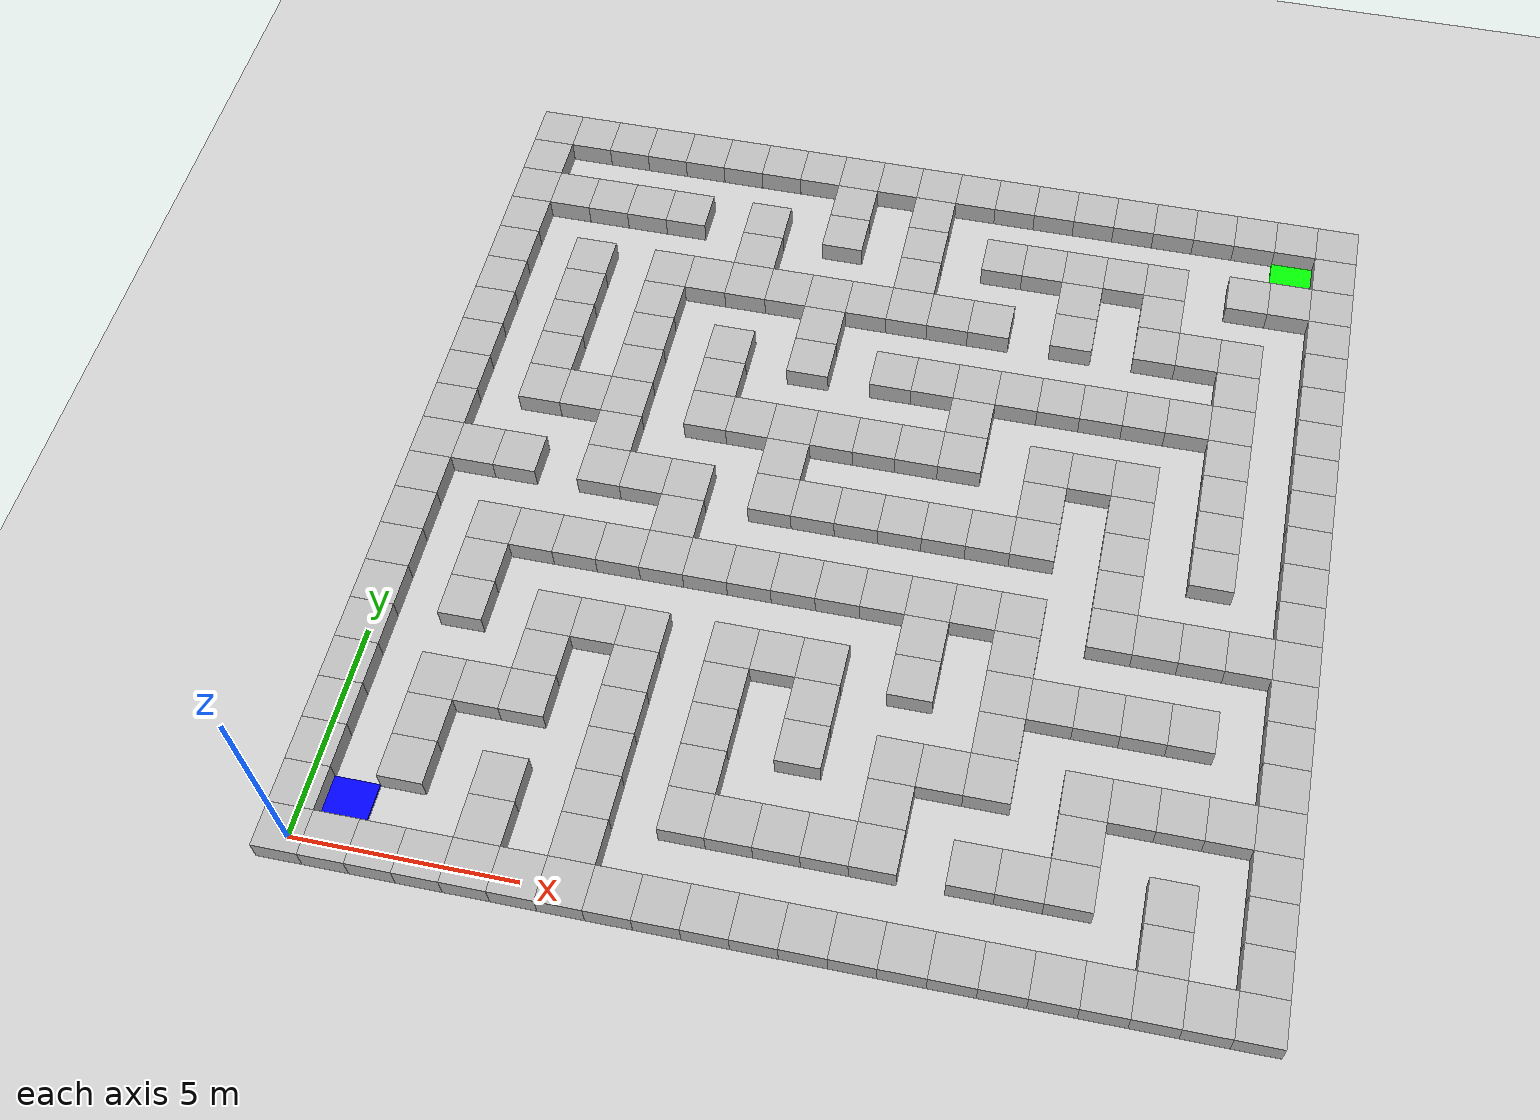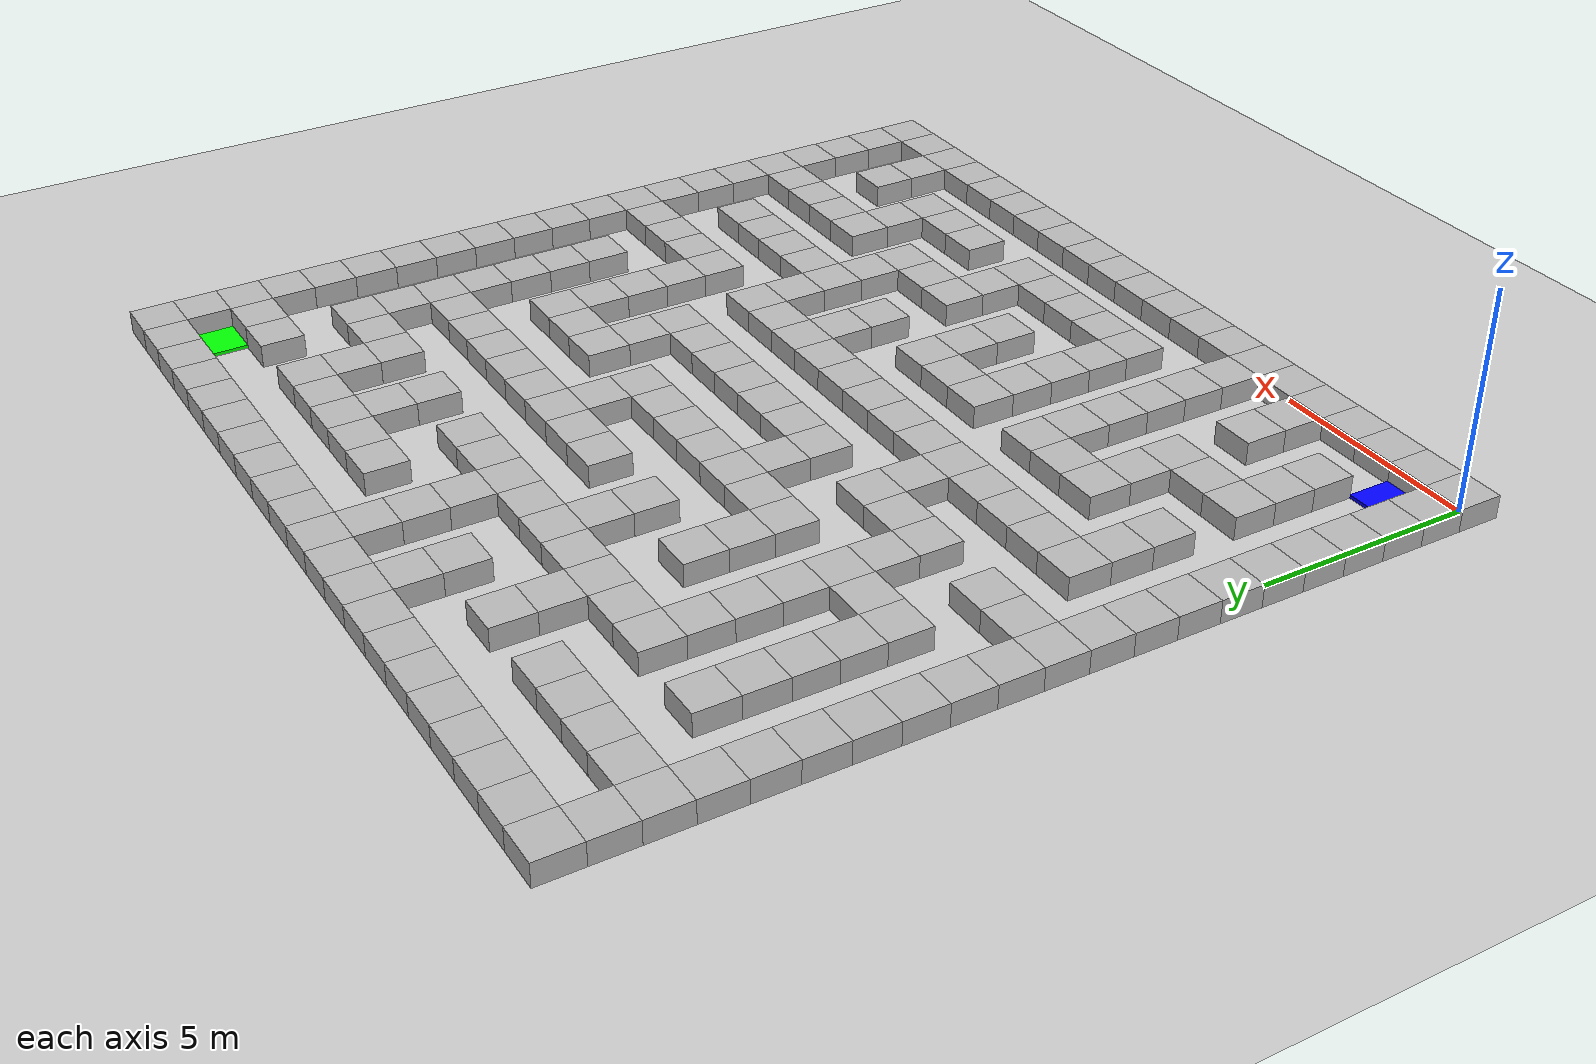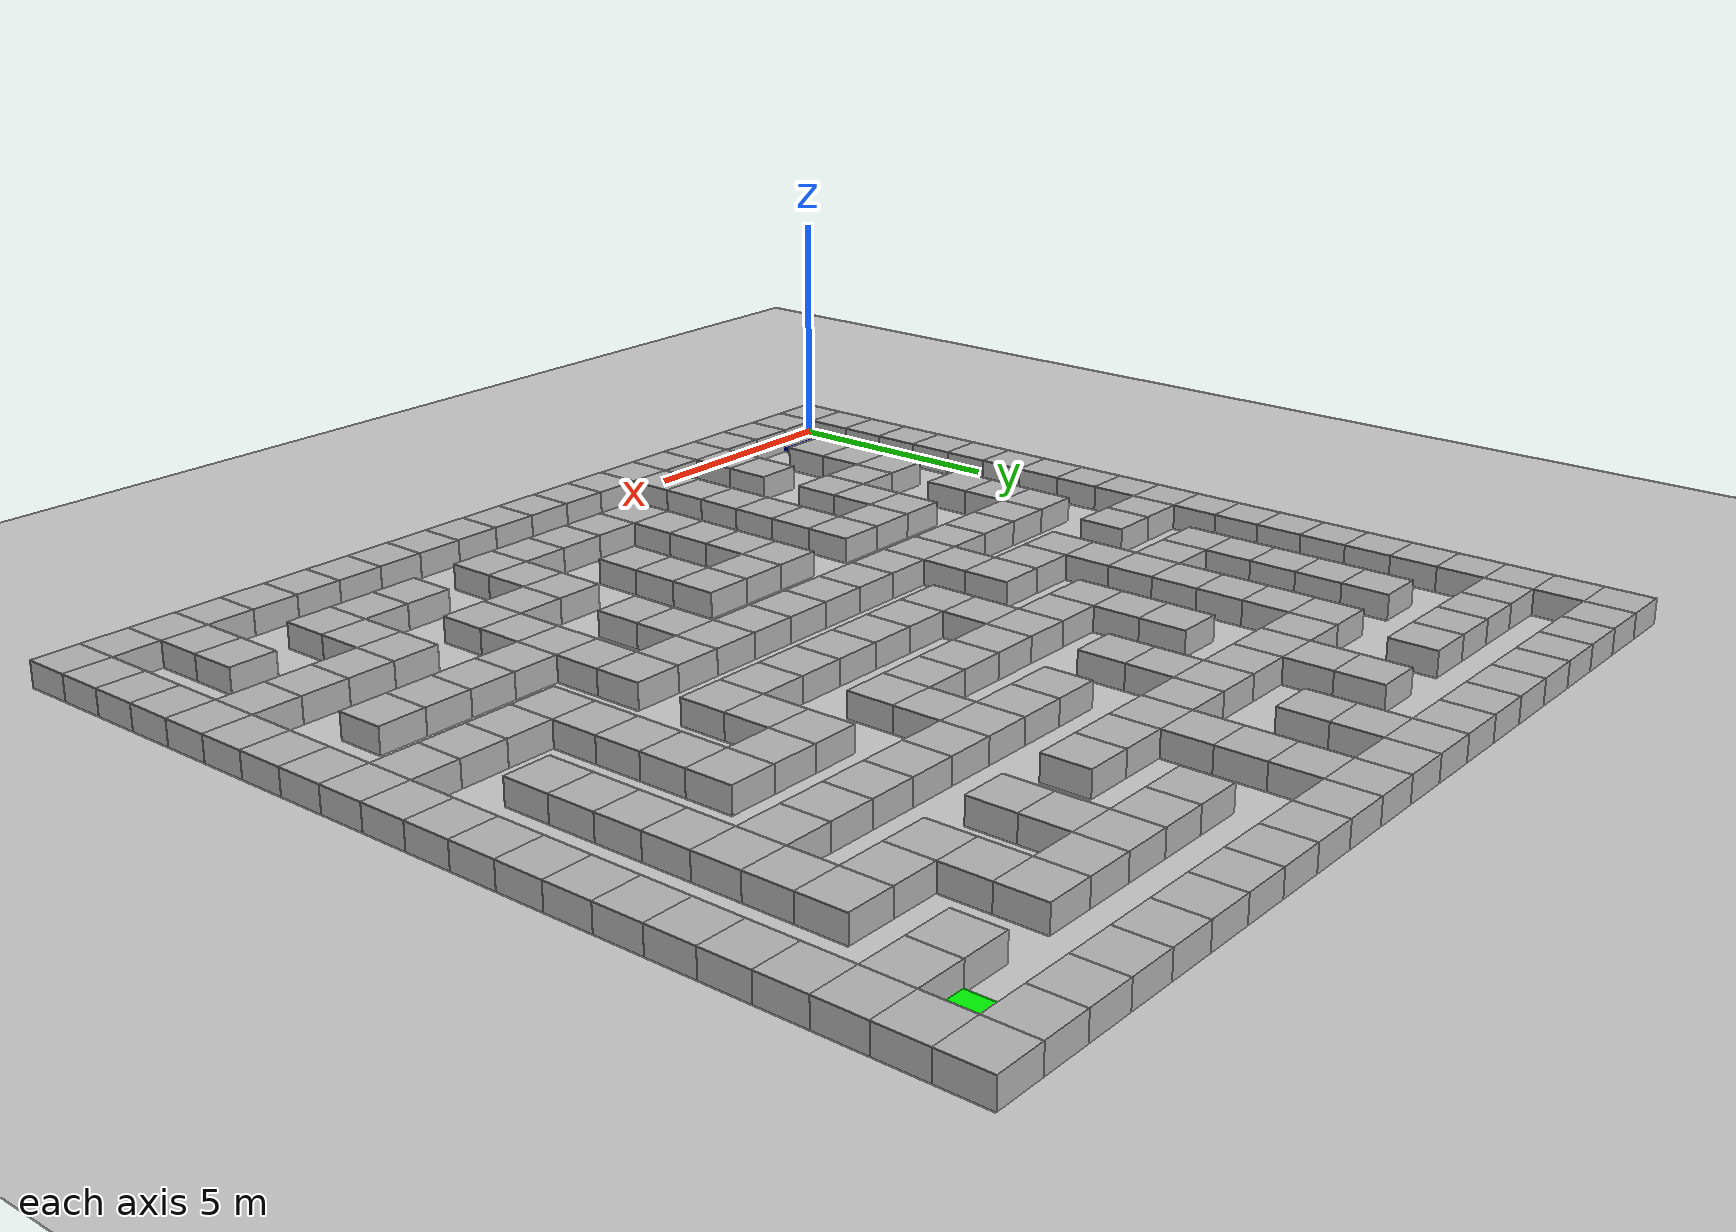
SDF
<sdf version='1.7'>
<world name="maze_world">
  <include>
    <uri>model://ground_plane</uri>
  </include>
  <include>
    <uri>model://sun</uri>
  </include>
  <model name="wall_0_0">
    <static>true</static>
    <pose>0 0 0 0 0 0</pose>
    <link name="link">
      <collision name="collision">
        <geometry>
          <box>
            <size>1 1 1</size>
          </box>
        </geometry>
      </collision>
      <visual name="visual">
        <geometry>
          <box>
            <size>1 1 1</size>
          </box>
        </geometry>
      </visual>
    </link>
  </model>
  <model name="wall_1_0">
    <static>true</static>
    <pose>1 0 0 0 0 0</pose>
    <link name="link">
      <collision name="collision">
        <geometry>
          <box>
            <size>1 1 1</size>
          </box>
        </geometry>
      </collision>
      <visual name="visual">
        <geometry>
          <box>
            <size>1 1 1</size>
          </box>
        </geometry>
      </visual>
    </link>
  </model>
  <model name="wall_2_0">
    <static>true</static>
    <pose>2 0 0 0 0 0</pose>
    <link name="link">
      <collision name="collision">
        <geometry>
          <box>
            <size>1 1 1</size>
          </box>
        </geometry>
      </collision>
      <visual name="visual">
        <geometry>
          <box>
            <size>1 1 1</size>
          </box>
        </geometry>
      </visual>
    </link>
  </model>
  <model name="wall_3_0">
    <static>true</static>
    <pose>3 0 0 0 0 0</pose>
    <link name="link">
      <collision name="collision">
        <geometry>
          <box>
            <size>1 1 1</size>
          </box>
        </geometry>
      </collision>
      <visual name="visual">
        <geometry>
          <box>
            <size>1 1 1</size>
          </box>
        </geometry>
      </visual>
    </link>
  </model>
  <model name="wall_4_0">
    <static>true</static>
    <pose>4 0 0 0 0 0</pose>
    <link name="link">
      <collision name="collision">
        <geometry>
          <box>
            <size>1 1 1</size>
          </box>
        </geometry>
      </collision>
      <visual name="visual">
        <geometry>
          <box>
            <size>1 1 1</size>
          </box>
        </geometry>
      </visual>
    </link>
  </model>
  <model name="wall_5_0">
    <static>true</static>
    <pose>5 0 0 0 0 0</pose>
    <link name="link">
      <collision name="collision">
        <geometry>
          <box>
            <size>1 1 1</size>
          </box>
        </geometry>
      </collision>
      <visual name="visual">
        <geometry>
          <box>
            <size>1 1 1</size>
          </box>
        </geometry>
      </visual>
    </link>
  </model>
  <model name="wall_6_0">
    <static>true</static>
    <pose>6 0 0 0 0 0</pose>
    <link name="link">
      <collision name="collision">
        <geometry>
          <box>
            <size>1 1 1</size>
          </box>
        </geometry>
      </collision>
      <visual name="visual">
        <geometry>
          <box>
            <size>1 1 1</size>
          </box>
        </geometry>
      </visual>
    </link>
  </model>
  <model name="wall_7_0">
    <static>true</static>
    <pose>7 0 0 0 0 0</pose>
    <link name="link">
      <collision name="collision">
        <geometry>
          <box>
            <size>1 1 1</size>
          </box>
        </geometry>
      </collision>
      <visual name="visual">
        <geometry>
          <box>
            <size>1 1 1</size>
          </box>
        </geometry>
      </visual>
    </link>
  </model>
  <model name="wall_8_0">
    <static>true</static>
    <pose>8 0 0 0 0 0</pose>
    <link name="link">
      <collision name="collision">
        <geometry>
          <box>
            <size>1 1 1</size>
          </box>
        </geometry>
      </collision>
      <visual name="visual">
        <geometry>
          <box>
            <size>1 1 1</size>
          </box>
        </geometry>
      </visual>
    </link>
  </model>
  <model name="wall_9_0">
    <static>true</static>
    <pose>9 0 0 0 0 0</pose>
    <link name="link">
      <collision name="collision">
        <geometry>
          <box>
            <size>1 1 1</size>
          </box>
        </geometry>
      </collision>
      <visual name="visual">
        <geometry>
          <box>
            <size>1 1 1</size>
          </box>
        </geometry>
      </visual>
    </link>
  </model>
  <model name="wall_10_0">
    <static>true</static>
    <pose>10 0 0 0 0 0</pose>
    <link name="link">
      <collision name="collision">
        <geometry>
          <box>
            <size>1 1 1</size>
          </box>
        </geometry>
      </collision>
      <visual name="visual">
        <geometry>
          <box>
            <size>1 1 1</size>
          </box>
        </geometry>
      </visual>
    </link>
  </model>
  <model name="wall_11_0">
    <static>true</static>
    <pose>11 0 0 0 0 0</pose>
    <link name="link">
      <collision name="collision">
        <geometry>
          <box>
            <size>1 1 1</size>
          </box>
        </geometry>
      </collision>
      <visual name="visual">
        <geometry>
          <box>
            <size>1 1 1</size>
          </box>
        </geometry>
      </visual>
    </link>
  </model>
  <model name="wall_12_0">
    <static>true</static>
    <pose>12 0 0 0 0 0</pose>
    <link name="link">
      <collision name="collision">
        <geometry>
          <box>
            <size>1 1 1</size>
          </box>
        </geometry>
      </collision>
      <visual name="visual">
        <geometry>
          <box>
            <size>1 1 1</size>
          </box>
        </geometry>
      </visual>
    </link>
  </model>
  <model name="wall_13_0">
    <static>true</static>
    <pose>13 0 0 0 0 0</pose>
    <link name="link">
      <collision name="collision">
        <geometry>
          <box>
            <size>1 1 1</size>
          </box>
        </geometry>
      </collision>
      <visual name="visual">
        <geometry>
          <box>
            <size>1 1 1</size>
          </box>
        </geometry>
      </visual>
    </link>
  </model>
  <model name="wall_14_0">
    <static>true</static>
    <pose>14 0 0 0 0 0</pose>
    <link name="link">
      <collision name="collision">
        <geometry>
          <box>
            <size>1 1 1</size>
          </box>
        </geometry>
      </collision>
      <visual name="visual">
        <geometry>
          <box>
            <size>1 1 1</size>
          </box>
        </geometry>
      </visual>
    </link>
  </model>
  <model name="wall_15_0">
    <static>true</static>
    <pose>15 0 0 0 0 0</pose>
    <link name="link">
      <collision name="collision">
        <geometry>
          <box>
            <size>1 1 1</size>
          </box>
        </geometry>
      </collision>
      <visual name="visual">
        <geometry>
          <box>
            <size>1 1 1</size>
          </box>
        </geometry>
      </visual>
    </link>
  </model>
  <model name="wall_16_0">
    <static>true</static>
    <pose>16 0 0 0 0 0</pose>
    <link name="link">
      <collision name="collision">
        <geometry>
          <box>
            <size>1 1 1</size>
          </box>
        </geometry>
      </collision>
      <visual name="visual">
        <geometry>
          <box>
            <size>1 1 1</size>
          </box>
        </geometry>
      </visual>
    </link>
  </model>
  <model name="wall_17_0">
    <static>true</static>
    <pose>17 0 0 0 0 0</pose>
    <link name="link">
      <collision name="collision">
        <geometry>
          <box>
            <size>1 1 1</size>
          </box>
        </geometry>
      </collision>
      <visual name="visual">
        <geometry>
          <box>
            <size>1 1 1</size>
          </box>
        </geometry>
      </visual>
    </link>
  </model>
  <model name="wall_18_0">
    <static>true</static>
    <pose>18 0 0 0 0 0</pose>
    <link name="link">
      <collision name="collision">
        <geometry>
          <box>
            <size>1 1 1</size>
          </box>
        </geometry>
      </collision>
      <visual name="visual">
        <geometry>
          <box>
            <size>1 1 1</size>
          </box>
        </geometry>
      </visual>
    </link>
  </model>
  <model name="wall_19_0">
    <static>true</static>
    <pose>19 0 0 0 0 0</pose>
    <link name="link">
      <collision name="collision">
        <geometry>
          <box>
            <size>1 1 1</size>
          </box>
        </geometry>
      </collision>
      <visual name="visual">
        <geometry>
          <box>
            <size>1 1 1</size>
          </box>
        </geometry>
      </visual>
    </link>
  </model>
  <model name="wall_20_0">
    <static>true</static>
    <pose>20 0 0 0 0 0</pose>
    <link name="link">
      <collision name="collision">
        <geometry>
          <box>
            <size>1 1 1</size>
          </box>
        </geometry>
      </collision>
      <visual name="visual">
        <geometry>
          <box>
            <size>1 1 1</size>
          </box>
        </geometry>
      </visual>
    </link>
  </model>
  <model name="wall_0_1">
    <static>true</static>
    <pose>0 1 0 0 0 0</pose>
    <link name="link">
      <collision name="collision">
        <geometry>
          <box>
            <size>1 1 1</size>
          </box>
        </geometry>
      </collision>
      <visual name="visual">
        <geometry>
          <box>
            <size>1 1 1</size>
          </box>
        </geometry>
      </visual>
    </link>
  </model>
  <model name="start_1_1">
    <static>true</static>
    <pose>1 1 0 0 0 0</pose>
    <link name="link">
      <collision name="collision">
        <geometry>
          <box>
            <size>1 1 0.001</size>
          </box>
        </geometry>
      </collision>
      <visual name="visual">
        <geometry>
          <box>
            <size>1 1 0.1</size>
          </box>
        </geometry>
        <material>
          <ambient>0 0 1 1</ambient>
        </material>
      </visual>
    </link>
  </model>
  <model name="wall_4_1">
    <static>true</static>
    <pose>4 1 0 0 0 0</pose>
    <link name="link">
      <collision name="collision">
        <geometry>
          <box>
            <size>1 1 1</size>
          </box>
        </geometry>
      </collision>
      <visual name="visual">
        <geometry>
          <box>
            <size>1 1 1</size>
          </box>
        </geometry>
      </visual>
    </link>
  </model>
  <model name="wall_6_1">
    <static>true</static>
    <pose>6 1 0 0 0 0</pose>
    <link name="link">
      <collision name="collision">
        <geometry>
          <box>
            <size>1 1 1</size>
          </box>
        </geometry>
      </collision>
      <visual name="visual">
        <geometry>
          <box>
            <size>1 1 1</size>
          </box>
        </geometry>
      </visual>
    </link>
  </model>
  <model name="wall_18_1">
    <static>true</static>
    <pose>18 1 0 0 0 0</pose>
    <link name="link">
      <collision name="collision">
        <geometry>
          <box>
            <size>1 1 1</size>
          </box>
        </geometry>
      </collision>
      <visual name="visual">
        <geometry>
          <box>
            <size>1 1 1</size>
          </box>
        </geometry>
      </visual>
    </link>
  </model>
  <model name="wall_20_1">
    <static>true</static>
    <pose>20 1 0 0 0 0</pose>
    <link name="link">
      <collision name="collision">
        <geometry>
          <box>
            <size>1 1 1</size>
          </box>
        </geometry>
      </collision>
      <visual name="visual">
        <geometry>
          <box>
            <size>1 1 1</size>
          </box>
        </geometry>
      </visual>
    </link>
  </model>
  <model name="wall_0_2">
    <static>true</static>
    <pose>0 2 0 0 0 0</pose>
    <link name="link">
      <collision name="collision">
        <geometry>
          <box>
            <size>1 1 1</size>
          </box>
        </geometry>
      </collision>
      <visual name="visual">
        <geometry>
          <box>
            <size>1 1 1</size>
          </box>
        </geometry>
      </visual>
    </link>
  </model>
  <model name="wall_2_2">
    <static>true</static>
    <pose>2 2 0 0 0 0</pose>
    <link name="link">
      <collision name="collision">
        <geometry>
          <box>
            <size>1 1 1</size>
          </box>
        </geometry>
      </collision>
      <visual name="visual">
        <geometry>
          <box>
            <size>1 1 1</size>
          </box>
        </geometry>
      </visual>
    </link>
  </model>
  <model name="wall_4_2">
    <static>true</static>
    <pose>4 2 0 0 0 0</pose>
    <link name="link">
      <collision name="collision">
        <geometry>
          <box>
            <size>1 1 1</size>
          </box>
        </geometry>
      </collision>
      <visual name="visual">
        <geometry>
          <box>
            <size>1 1 1</size>
          </box>
        </geometry>
      </visual>
    </link>
  </model>
  <model name="wall_6_2">
    <static>true</static>
    <pose>6 2 0 0 0 0</pose>
    <link name="link">
      <collision name="collision">
        <geometry>
          <box>
            <size>1 1 1</size>
          </box>
        </geometry>
      </collision>
      <visual name="visual">
        <geometry>
          <box>
            <size>1 1 1</size>
          </box>
        </geometry>
      </visual>
    </link>
  </model>
  <model name="wall_8_2">
    <static>true</static>
    <pose>8 2 0 0 0 0</pose>
    <link name="link">
      <collision name="collision">
        <geometry>
          <box>
            <size>1 1 1</size>
          </box>
        </geometry>
      </collision>
      <visual name="visual">
        <geometry>
          <box>
            <size>1 1 1</size>
          </box>
        </geometry>
      </visual>
    </link>
  </model>
  <model name="wall_9_2">
    <static>true</static>
    <pose>9 2 0 0 0 0</pose>
    <link name="link">
      <collision name="collision">
        <geometry>
          <box>
            <size>1 1 1</size>
          </box>
        </geometry>
      </collision>
      <visual name="visual">
        <geometry>
          <box>
            <size>1 1 1</size>
          </box>
        </geometry>
      </visual>
    </link>
  </model>
  <model name="wall_10_2">
    <static>true</static>
    <pose>10 2 0 0 0 0</pose>
    <link name="link">
      <collision name="collision">
        <geometry>
          <box>
            <size>1 1 1</size>
          </box>
        </geometry>
      </collision>
      <visual name="visual">
        <geometry>
          <box>
            <size>1 1 1</size>
          </box>
        </geometry>
      </visual>
    </link>
  </model>
  <model name="wall_11_2">
    <static>true</static>
    <pose>11 2 0 0 0 0</pose>
    <link name="link">
      <collision name="collision">
        <geometry>
          <box>
            <size>1 1 1</size>
          </box>
        </geometry>
      </collision>
      <visual name="visual">
        <geometry>
          <box>
            <size>1 1 1</size>
          </box>
        </geometry>
      </visual>
    </link>
  </model>
  <model name="wall_12_2">
    <static>true</static>
    <pose>12 2 0 0 0 0</pose>
    <link name="link">
      <collision name="collision">
        <geometry>
          <box>
            <size>1 1 1</size>
          </box>
        </geometry>
      </collision>
      <visual name="visual">
        <geometry>
          <box>
            <size>1 1 1</size>
          </box>
        </geometry>
      </visual>
    </link>
  </model>
  <model name="wall_14_2">
    <static>true</static>
    <pose>14 2 0 0 0 0</pose>
    <link name="link">
      <collision name="collision">
        <geometry>
          <box>
            <size>1 1 1</size>
          </box>
        </geometry>
      </collision>
      <visual name="visual">
        <geometry>
          <box>
            <size>1 1 1</size>
          </box>
        </geometry>
      </visual>
    </link>
  </model>
  <model name="wall_15_2">
    <static>true</static>
    <pose>15 2 0 0 0 0</pose>
    <link name="link">
      <collision name="collision">
        <geometry>
          <box>
            <size>1 1 1</size>
          </box>
        </geometry>
      </collision>
      <visual name="visual">
        <geometry>
          <box>
            <size>1 1 1</size>
          </box>
        </geometry>
      </visual>
    </link>
  </model>
  <model name="wall_16_2">
    <static>true</static>
    <pose>16 2 0 0 0 0</pose>
    <link name="link">
      <collision name="collision">
        <geometry>
          <box>
            <size>1 1 1</size>
          </box>
        </geometry>
      </collision>
      <visual name="visual">
        <geometry>
          <box>
            <size>1 1 1</size>
          </box>
        </geometry>
      </visual>
    </link>
  </model>
  <model name="wall_18_2">
    <static>true</static>
    <pose>18 2 0 0 0 0</pose>
    <link name="link">
      <collision name="collision">
        <geometry>
          <box>
            <size>1 1 1</size>
          </box>
        </geometry>
      </collision>
      <visual name="visual">
        <geometry>
          <box>
            <size>1 1 1</size>
          </box>
        </geometry>
      </visual>
    </link>
  </model>
  <model name="wall_20_2">
    <static>true</static>
    <pose>20 2 0 0 0 0</pose>
    <link name="link">
      <collision name="collision">
        <geometry>
          <box>
            <size>1 1 1</size>
          </box>
        </geometry>
      </collision>
      <visual name="visual">
        <geometry>
          <box>
            <size>1 1 1</size>
          </box>
        </geometry>
      </visual>
    </link>
  </model>
  <model name="wall_0_3">
    <static>true</static>
    <pose>0 3 0 0 0 0</pose>
    <link name="link">
      <collision name="collision">
        <geometry>
          <box>
            <size>1 1 1</size>
          </box>
        </geometry>
      </collision>
      <visual name="visual">
        <geometry>
          <box>
            <size>1 1 1</size>
          </box>
        </geometry>
      </visual>
    </link>
  </model>
  <model name="wall_2_3">
    <static>true</static>
    <pose>2 3 0 0 0 0</pose>
    <link name="link">
      <collision name="collision">
        <geometry>
          <box>
            <size>1 1 1</size>
          </box>
        </geometry>
      </collision>
      <visual name="visual">
        <geometry>
          <box>
            <size>1 1 1</size>
          </box>
        </geometry>
      </visual>
    </link>
  </model>
  <model name="wall_6_3">
    <static>true</static>
    <pose>6 3 0 0 0 0</pose>
    <link name="link">
      <collision name="collision">
        <geometry>
          <box>
            <size>1 1 1</size>
          </box>
        </geometry>
      </collision>
      <visual name="visual">
        <geometry>
          <box>
            <size>1 1 1</size>
          </box>
        </geometry>
      </visual>
    </link>
  </model>
  <model name="wall_8_3">
    <static>true</static>
    <pose>8 3 0 0 0 0</pose>
    <link name="link">
      <collision name="collision">
        <geometry>
          <box>
            <size>1 1 1</size>
          </box>
        </geometry>
      </collision>
      <visual name="visual">
        <geometry>
          <box>
            <size>1 1 1</size>
          </box>
        </geometry>
      </visual>
    </link>
  </model>
  <model name="wall_12_3">
    <static>true</static>
    <pose>12 3 0 0 0 0</pose>
    <link name="link">
      <collision name="collision">
        <geometry>
          <box>
            <size>1 1 1</size>
          </box>
        </geometry>
      </collision>
      <visual name="visual">
        <geometry>
          <box>
            <size>1 1 1</size>
          </box>
        </geometry>
      </visual>
    </link>
  </model>
  <model name="wall_16_3">
    <static>true</static>
    <pose>16 3 0 0 0 0</pose>
    <link name="link">
      <collision name="collision">
        <geometry>
          <box>
            <size>1 1 1</size>
          </box>
        </geometry>
      </collision>
      <visual name="visual">
        <geometry>
          <box>
            <size>1 1 1</size>
          </box>
        </geometry>
      </visual>
    </link>
  </model>
  <model name="wall_20_3">
    <static>true</static>
    <pose>20 3 0 0 0 0</pose>
    <link name="link">
      <collision name="collision">
        <geometry>
          <box>
            <size>1 1 1</size>
          </box>
        </geometry>
      </collision>
      <visual name="visual">
        <geometry>
          <box>
            <size>1 1 1</size>
          </box>
        </geometry>
      </visual>
    </link>
  </model>
  <model name="wall_0_4">
    <static>true</static>
    <pose>0 4 0 0 0 0</pose>
    <link name="link">
      <collision name="collision">
        <geometry>
          <box>
            <size>1 1 1</size>
          </box>
        </geometry>
      </collision>
      <visual name="visual">
        <geometry>
          <box>
            <size>1 1 1</size>
          </box>
        </geometry>
      </visual>
    </link>
  </model>
  <model name="wall_2_4">
    <static>true</static>
    <pose>2 4 0 0 0 0</pose>
    <link name="link">
      <collision name="collision">
        <geometry>
          <box>
            <size>1 1 1</size>
          </box>
        </geometry>
      </collision>
      <visual name="visual">
        <geometry>
          <box>
            <size>1 1 1</size>
          </box>
        </geometry>
      </visual>
    </link>
  </model>
  <model name="wall_3_4">
    <static>true</static>
    <pose>3 4 0 0 0 0</pose>
    <link name="link">
      <collision name="collision">
        <geometry>
          <box>
            <size>1 1 1</size>
          </box>
        </geometry>
      </collision>
      <visual name="visual">
        <geometry>
          <box>
            <size>1 1 1</size>
          </box>
        </geometry>
      </visual>
    </link>
  </model>
  <model name="wall_4_4">
    <static>true</static>
    <pose>4 4 0 0 0 0</pose>
    <link name="link">
      <collision name="collision">
        <geometry>
          <box>
            <size>1 1 1</size>
          </box>
        </geometry>
      </collision>
      <visual name="visual">
        <geometry>
          <box>
            <size>1 1 1</size>
          </box>
        </geometry>
      </visual>
    </link>
  </model>
  <model name="wall_6_4">
    <static>true</static>
    <pose>6 4 0 0 0 0</pose>
    <link name="link">
      <collision name="collision">
        <geometry>
          <box>
            <size>1 1 1</size>
          </box>
        </geometry>
      </collision>
      <visual name="visual">
        <geometry>
          <box>
            <size>1 1 1</size>
          </box>
        </geometry>
      </visual>
    </link>
  </model>
  <model name="wall_8_4">
    <static>true</static>
    <pose>8 4 0 0 0 0</pose>
    <link name="link">
      <collision name="collision">
        <geometry>
          <box>
            <size>1 1 1</size>
          </box>
        </geometry>
      </collision>
      <visual name="visual">
        <geometry>
          <box>
            <size>1 1 1</size>
          </box>
        </geometry>
      </visual>
    </link>
  </model>
  <model name="wall_10_4">
    <static>true</static>
    <pose>10 4 0 0 0 0</pose>
    <link name="link">
      <collision name="collision">
        <geometry>
          <box>
            <size>1 1 1</size>
          </box>
        </geometry>
      </collision>
      <visual name="visual">
        <geometry>
          <box>
            <size>1 1 1</size>
          </box>
        </geometry>
      </visual>
    </link>
  </model>
  <model name="wall_12_4">
    <static>true</static>
    <pose>12 4 0 0 0 0</pose>
    <link name="link">
      <collision name="collision">
        <geometry>
          <box>
            <size>1 1 1</size>
          </box>
        </geometry>
      </collision>
      <visual name="visual">
        <geometry>
          <box>
            <size>1 1 1</size>
          </box>
        </geometry>
      </visual>
    </link>
  </model>
  <model name="wall_13_4">
    <static>true</static>
    <pose>13 4 0 0 0 0</pose>
    <link name="link">
      <collision name="collision">
        <geometry>
          <box>
            <size>1 1 1</size>
          </box>
        </geometry>
      </collision>
      <visual name="visual">
        <geometry>
          <box>
            <size>1 1 1</size>
          </box>
        </geometry>
      </visual>
    </link>
  </model>
  <model name="wall_14_4">
    <static>true</static>
    <pose>14 4 0 0 0 0</pose>
    <link name="link">
      <collision name="collision">
        <geometry>
          <box>
            <size>1 1 1</size>
          </box>
        </geometry>
      </collision>
      <visual name="visual">
        <geometry>
          <box>
            <size>1 1 1</size>
          </box>
        </geometry>
      </visual>
    </link>
  </model>
  <model name="wall_16_4">
    <static>true</static>
    <pose>16 4 0 0 0 0</pose>
    <link name="link">
      <collision name="collision">
        <geometry>
          <box>
            <size>1 1 1</size>
          </box>
        </geometry>
      </collision>
      <visual name="visual">
        <geometry>
          <box>
            <size>1 1 1</size>
          </box>
        </geometry>
      </visual>
    </link>
  </model>
  <model name="wall_17_4">
    <static>true</static>
    <pose>17 4 0 0 0 0</pose>
    <link name="link">
      <collision name="collision">
        <geometry>
          <box>
            <size>1 1 1</size>
          </box>
        </geometry>
      </collision>
      <visual name="visual">
        <geometry>
          <box>
            <size>1 1 1</size>
          </box>
        </geometry>
      </visual>
    </link>
  </model>
  <model name="wall_18_4">
    <static>true</static>
    <pose>18 4 0 0 0 0</pose>
    <link name="link">
      <collision name="collision">
        <geometry>
          <box>
            <size>1 1 1</size>
          </box>
        </geometry>
      </collision>
      <visual name="visual">
        <geometry>
          <box>
            <size>1 1 1</size>
          </box>
        </geometry>
      </visual>
    </link>
  </model>
  <model name="wall_19_4">
    <static>true</static>
    <pose>19 4 0 0 0 0</pose>
    <link name="link">
      <collision name="collision">
        <geometry>
          <box>
            <size>1 1 1</size>
          </box>
        </geometry>
      </collision>
      <visual name="visual">
        <geometry>
          <box>
            <size>1 1 1</size>
          </box>
        </geometry>
      </visual>
    </link>
  </model>
  <model name="wall_20_4">
    <static>true</static>
    <pose>20 4 0 0 0 0</pose>
    <link name="link">
      <collision name="collision">
        <geometry>
          <box>
            <size>1 1 1</size>
          </box>
        </geometry>
      </collision>
      <visual name="visual">
        <geometry>
          <box>
            <size>1 1 1</size>
          </box>
        </geometry>
      </visual>
    </link>
  </model>
  <model name="wall_0_5">
    <static>true</static>
    <pose>0 5 0 0 0 0</pose>
    <link name="link">
      <collision name="collision">
        <geometry>
          <box>
            <size>1 1 1</size>
          </box>
        </geometry>
      </collision>
      <visual name="visual">
        <geometry>
          <box>
            <size>1 1 1</size>
          </box>
        </geometry>
      </visual>
    </link>
  </model>
  <model name="wall_4_5">
    <static>true</static>
    <pose>4 5 0 0 0 0</pose>
    <link name="link">
      <collision name="collision">
        <geometry>
          <box>
            <size>1 1 1</size>
          </box>
        </geometry>
      </collision>
      <visual name="visual">
        <geometry>
          <box>
            <size>1 1 1</size>
          </box>
        </geometry>
      </visual>
    </link>
  </model>
  <model name="wall_6_5">
    <static>true</static>
    <pose>6 5 0 0 0 0</pose>
    <link name="link">
      <collision name="collision">
        <geometry>
          <box>
            <size>1 1 1</size>
          </box>
        </geometry>
      </collision>
      <visual name="visual">
        <geometry>
          <box>
            <size>1 1 1</size>
          </box>
        </geometry>
      </visual>
    </link>
  </model>
  <model name="wall_8_5">
    <static>true</static>
    <pose>8 5 0 0 0 0</pose>
    <link name="link">
      <collision name="collision">
        <geometry>
          <box>
            <size>1 1 1</size>
          </box>
        </geometry>
      </collision>
      <visual name="visual">
        <geometry>
          <box>
            <size>1 1 1</size>
          </box>
        </geometry>
      </visual>
    </link>
  </model>
  <model name="wall_10_5">
    <static>true</static>
    <pose>10 5 0 0 0 0</pose>
    <link name="link">
      <collision name="collision">
        <geometry>
          <box>
            <size>1 1 1</size>
          </box>
        </geometry>
      </collision>
      <visual name="visual">
        <geometry>
          <box>
            <size>1 1 1</size>
          </box>
        </geometry>
      </visual>
    </link>
  </model>
  <model name="wall_14_5">
    <static>true</static>
    <pose>14 5 0 0 0 0</pose>
    <link name="link">
      <collision name="collision">
        <geometry>
          <box>
            <size>1 1 1</size>
          </box>
        </geometry>
      </collision>
      <visual name="visual">
        <geometry>
          <box>
            <size>1 1 1</size>
          </box>
        </geometry>
      </visual>
    </link>
  </model>
  <model name="wall_20_5">
    <static>true</static>
    <pose>20 5 0 0 0 0</pose>
    <link name="link">
      <collision name="collision">
        <geometry>
          <box>
            <size>1 1 1</size>
          </box>
        </geometry>
      </collision>
      <visual name="visual">
        <geometry>
          <box>
            <size>1 1 1</size>
          </box>
        </geometry>
      </visual>
    </link>
  </model>
  <model name="wall_0_6">
    <static>true</static>
    <pose>0 6 0 0 0 0</pose>
    <link name="link">
      <collision name="collision">
        <geometry>
          <box>
            <size>1 1 1</size>
          </box>
        </geometry>
      </collision>
      <visual name="visual">
        <geometry>
          <box>
            <size>1 1 1</size>
          </box>
        </geometry>
      </visual>
    </link>
  </model>
  <model name="wall_2_6">
    <static>true</static>
    <pose>2 6 0 0 0 0</pose>
    <link name="link">
      <collision name="collision">
        <geometry>
          <box>
            <size>1 1 1</size>
          </box>
        </geometry>
      </collision>
      <visual name="visual">
        <geometry>
          <box>
            <size>1 1 1</size>
          </box>
        </geometry>
      </visual>
    </link>
  </model>
  <model name="wall_4_6">
    <static>true</static>
    <pose>4 6 0 0 0 0</pose>
    <link name="link">
      <collision name="collision">
        <geometry>
          <box>
            <size>1 1 1</size>
          </box>
        </geometry>
      </collision>
      <visual name="visual">
        <geometry>
          <box>
            <size>1 1 1</size>
          </box>
        </geometry>
      </visual>
    </link>
  </model>
  <model name="wall_5_6">
    <static>true</static>
    <pose>5 6 0 0 0 0</pose>
    <link name="link">
      <collision name="collision">
        <geometry>
          <box>
            <size>1 1 1</size>
          </box>
        </geometry>
      </collision>
      <visual name="visual">
        <geometry>
          <box>
            <size>1 1 1</size>
          </box>
        </geometry>
      </visual>
    </link>
  </model>
  <model name="wall_6_6">
    <static>true</static>
    <pose>6 6 0 0 0 0</pose>
    <link name="link">
      <collision name="collision">
        <geometry>
          <box>
            <size>1 1 1</size>
          </box>
        </geometry>
      </collision>
      <visual name="visual">
        <geometry>
          <box>
            <size>1 1 1</size>
          </box>
        </geometry>
      </visual>
    </link>
  </model>
  <model name="wall_8_6">
    <static>true</static>
    <pose>8 6 0 0 0 0</pose>
    <link name="link">
      <collision name="collision">
        <geometry>
          <box>
            <size>1 1 1</size>
          </box>
        </geometry>
      </collision>
      <visual name="visual">
        <geometry>
          <box>
            <size>1 1 1</size>
          </box>
        </geometry>
      </visual>
    </link>
  </model>
  <model name="wall_9_6">
    <static>true</static>
    <pose>9 6 0 0 0 0</pose>
    <link name="link">
      <collision name="collision">
        <geometry>
          <box>
            <size>1 1 1</size>
          </box>
        </geometry>
      </collision>
      <visual name="visual">
        <geometry>
          <box>
            <size>1 1 1</size>
          </box>
        </geometry>
      </visual>
    </link>
  </model>
  <model name="wall_10_6">
    <static>true</static>
    <pose>10 6 0 0 0 0</pose>
    <link name="link">
      <collision name="collision">
        <geometry>
          <box>
            <size>1 1 1</size>
          </box>
        </geometry>
      </collision>
      <visual name="visual">
        <geometry>
          <box>
            <size>1 1 1</size>
          </box>
        </geometry>
      </visual>
    </link>
  </model>
  <model name="wall_12_6">
    <static>true</static>
    <pose>12 6 0 0 0 0</pose>
    <link name="link">
      <collision name="collision">
        <geometry>
          <box>
            <size>1 1 1</size>
          </box>
        </geometry>
      </collision>
      <visual name="visual">
        <geometry>
          <box>
            <size>1 1 1</size>
          </box>
        </geometry>
      </visual>
    </link>
  </model>
  <model name="wall_14_6">
    <static>true</static>
    <pose>14 6 0 0 0 0</pose>
    <link name="link">
      <collision name="collision">
        <geometry>
          <box>
            <size>1 1 1</size>
          </box>
        </geometry>
      </collision>
      <visual name="visual">
        <geometry>
          <box>
            <size>1 1 1</size>
          </box>
        </geometry>
      </visual>
    </link>
  </model>
  <model name="wall_15_6">
    <static>true</static>
    <pose>15 6 0 0 0 0</pose>
    <link name="link">
      <collision name="collision">
        <geometry>
          <box>
            <size>1 1 1</size>
          </box>
        </geometry>
      </collision>
      <visual name="visual">
        <geometry>
          <box>
            <size>1 1 1</size>
          </box>
        </geometry>
      </visual>
    </link>
  </model>
  <model name="wall_16_6">
    <static>true</static>
    <pose>16 6 0 0 0 0</pose>
    <link name="link">
      <collision name="collision">
        <geometry>
          <box>
            <size>1 1 1</size>
          </box>
        </geometry>
      </collision>
      <visual name="visual">
        <geometry>
          <box>
            <size>1 1 1</size>
          </box>
        </geometry>
      </visual>
    </link>
  </model>
  <model name="wall_17_6">
    <static>true</static>
    <pose>17 6 0 0 0 0</pose>
    <link name="link">
      <collision name="collision">
        <geometry>
          <box>
            <size>1 1 1</size>
          </box>
        </geometry>
      </collision>
      <visual name="visual">
        <geometry>
          <box>
            <size>1 1 1</size>
          </box>
        </geometry>
      </visual>
    </link>
  </model>
  <model name="wall_18_6">
    <static>true</static>
    <pose>18 6 0 0 0 0</pose>
    <link name="link">
      <collision name="collision">
        <geometry>
          <box>
            <size>1 1 1</size>
          </box>
        </geometry>
      </collision>
      <visual name="visual">
        <geometry>
          <box>
            <size>1 1 1</size>
          </box>
        </geometry>
      </visual>
    </link>
  </model>
  <model name="wall_20_6">
    <static>true</static>
    <pose>20 6 0 0 0 0</pose>
    <link name="link">
      <collision name="collision">
        <geometry>
          <box>
            <size>1 1 1</size>
          </box>
        </geometry>
      </collision>
      <visual name="visual">
        <geometry>
          <box>
            <size>1 1 1</size>
          </box>
        </geometry>
      </visual>
    </link>
  </model>
  <model name="wall_0_7">
    <static>true</static>
    <pose>0 7 0 0 0 0</pose>
    <link name="link">
      <collision name="collision">
        <geometry>
          <box>
            <size>1 1 1</size>
          </box>
        </geometry>
      </collision>
      <visual name="visual">
        <geometry>
          <box>
            <size>1 1 1</size>
          </box>
        </geometry>
      </visual>
    </link>
  </model>
  <model name="wall_2_7">
    <static>true</static>
    <pose>2 7 0 0 0 0</pose>
    <link name="link">
      <collision name="collision">
        <geometry>
          <box>
            <size>1 1 1</size>
          </box>
        </geometry>
      </collision>
      <visual name="visual">
        <geometry>
          <box>
            <size>1 1 1</size>
          </box>
        </geometry>
      </visual>
    </link>
  </model>
  <model name="wall_12_7">
    <static>true</static>
    <pose>12 7 0 0 0 0</pose>
    <link name="link">
      <collision name="collision">
        <geometry>
          <box>
            <size>1 1 1</size>
          </box>
        </geometry>
      </collision>
      <visual name="visual">
        <geometry>
          <box>
            <size>1 1 1</size>
          </box>
        </geometry>
      </visual>
    </link>
  </model>
  <model name="wall_14_7">
    <static>true</static>
    <pose>14 7 0 0 0 0</pose>
    <link name="link">
      <collision name="collision">
        <geometry>
          <box>
            <size>1 1 1</size>
          </box>
        </geometry>
      </collision>
      <visual name="visual">
        <geometry>
          <box>
            <size>1 1 1</size>
          </box>
        </geometry>
      </visual>
    </link>
  </model>
  <model name="wall_20_7">
    <static>true</static>
    <pose>20 7 0 0 0 0</pose>
    <link name="link">
      <collision name="collision">
        <geometry>
          <box>
            <size>1 1 1</size>
          </box>
        </geometry>
      </collision>
      <visual name="visual">
        <geometry>
          <box>
            <size>1 1 1</size>
          </box>
        </geometry>
      </visual>
    </link>
  </model>
  <model name="wall_0_8">
    <static>true</static>
    <pose>0 8 0 0 0 0</pose>
    <link name="link">
      <collision name="collision">
        <geometry>
          <box>
            <size>1 1 1</size>
          </box>
        </geometry>
      </collision>
      <visual name="visual">
        <geometry>
          <box>
            <size>1 1 1</size>
          </box>
        </geometry>
      </visual>
    </link>
  </model>
  <model name="wall_2_8">
    <static>true</static>
    <pose>2 8 0 0 0 0</pose>
    <link name="link">
      <collision name="collision">
        <geometry>
          <box>
            <size>1 1 1</size>
          </box>
        </geometry>
      </collision>
      <visual name="visual">
        <geometry>
          <box>
            <size>1 1 1</size>
          </box>
        </geometry>
      </visual>
    </link>
  </model>
  <model name="wall_3_8">
    <static>true</static>
    <pose>3 8 0 0 0 0</pose>
    <link name="link">
      <collision name="collision">
        <geometry>
          <box>
            <size>1 1 1</size>
          </box>
        </geometry>
      </collision>
      <visual name="visual">
        <geometry>
          <box>
            <size>1 1 1</size>
          </box>
        </geometry>
      </visual>
    </link>
  </model>
  <model name="wall_4_8">
    <static>true</static>
    <pose>4 8 0 0 0 0</pose>
    <link name="link">
      <collision name="collision">
        <geometry>
          <box>
            <size>1 1 1</size>
          </box>
        </geometry>
      </collision>
      <visual name="visual">
        <geometry>
          <box>
            <size>1 1 1</size>
          </box>
        </geometry>
      </visual>
    </link>
  </model>
  <model name="wall_5_8">
    <static>true</static>
    <pose>5 8 0 0 0 0</pose>
    <link name="link">
      <collision name="collision">
        <geometry>
          <box>
            <size>1 1 1</size>
          </box>
        </geometry>
      </collision>
      <visual name="visual">
        <geometry>
          <box>
            <size>1 1 1</size>
          </box>
        </geometry>
      </visual>
    </link>
  </model>
  <model name="wall_6_8">
    <static>true</static>
    <pose>6 8 0 0 0 0</pose>
    <link name="link">
      <collision name="collision">
        <geometry>
          <box>
            <size>1 1 1</size>
          </box>
        </geometry>
      </collision>
      <visual name="visual">
        <geometry>
          <box>
            <size>1 1 1</size>
          </box>
        </geometry>
      </visual>
    </link>
  </model>
  <model name="wall_7_8">
    <static>true</static>
    <pose>7 8 0 0 0 0</pose>
    <link name="link">
      <collision name="collision">
        <geometry>
          <box>
            <size>1 1 1</size>
          </box>
        </geometry>
      </collision>
      <visual name="visual">
        <geometry>
          <box>
            <size>1 1 1</size>
          </box>
        </geometry>
      </visual>
    </link>
  </model>
  <model name="wall_8_8">
    <static>true</static>
    <pose>8 8 0 0 0 0</pose>
    <link name="link">
      <collision name="collision">
        <geometry>
          <box>
            <size>1 1 1</size>
          </box>
        </geometry>
      </collision>
      <visual name="visual">
        <geometry>
          <box>
            <size>1 1 1</size>
          </box>
        </geometry>
      </visual>
    </link>
  </model>
  <model name="wall_9_8">
    <static>true</static>
    <pose>9 8 0 0 0 0</pose>
    <link name="link">
      <collision name="collision">
        <geometry>
          <box>
            <size>1 1 1</size>
          </box>
        </geometry>
      </collision>
      <visual name="visual">
        <geometry>
          <box>
            <size>1 1 1</size>
          </box>
        </geometry>
      </visual>
    </link>
  </model>
  <model name="wall_10_8">
    <static>true</static>
    <pose>10 8 0 0 0 0</pose>
    <link name="link">
      <collision name="collision">
        <geometry>
          <box>
            <size>1 1 1</size>
          </box>
        </geometry>
      </collision>
      <visual name="visual">
        <geometry>
          <box>
            <size>1 1 1</size>
          </box>
        </geometry>
      </visual>
    </link>
  </model>
  <model name="wall_11_8">
    <static>true</static>
    <pose>11 8 0 0 0 0</pose>
    <link name="link">
      <collision name="collision">
        <geometry>
          <box>
            <size>1 1 1</size>
          </box>
        </geometry>
      </collision>
      <visual name="visual">
        <geometry>
          <box>
            <size>1 1 1</size>
          </box>
        </geometry>
      </visual>
    </link>
  </model>
  <model name="wall_12_8">
    <static>true</static>
    <pose>12 8 0 0 0 0</pose>
    <link name="link">
      <collision name="collision">
        <geometry>
          <box>
            <size>1 1 1</size>
          </box>
        </geometry>
      </collision>
      <visual name="visual">
        <geometry>
          <box>
            <size>1 1 1</size>
          </box>
        </geometry>
      </visual>
    </link>
  </model>
  <model name="wall_13_8">
    <static>true</static>
    <pose>13 8 0 0 0 0</pose>
    <link name="link">
      <collision name="collision">
        <geometry>
          <box>
            <size>1 1 1</size>
          </box>
        </geometry>
      </collision>
      <visual name="visual">
        <geometry>
          <box>
            <size>1 1 1</size>
          </box>
        </geometry>
      </visual>
    </link>
  </model>
  <model name="wall_14_8">
    <static>true</static>
    <pose>14 8 0 0 0 0</pose>
    <link name="link">
      <collision name="collision">
        <geometry>
          <box>
            <size>1 1 1</size>
          </box>
        </geometry>
      </collision>
      <visual name="visual">
        <geometry>
          <box>
            <size>1 1 1</size>
          </box>
        </geometry>
      </visual>
    </link>
  </model>
  <model name="wall_16_8">
    <static>true</static>
    <pose>16 8 0 0 0 0</pose>
    <link name="link">
      <collision name="collision">
        <geometry>
          <box>
            <size>1 1 1</size>
          </box>
        </geometry>
      </collision>
      <visual name="visual">
        <geometry>
          <box>
            <size>1 1 1</size>
          </box>
        </geometry>
      </visual>
    </link>
  </model>
  <model name="wall_17_8">
    <static>true</static>
    <pose>17 8 0 0 0 0</pose>
    <link name="link">
      <collision name="collision">
        <geometry>
          <box>
            <size>1 1 1</size>
          </box>
        </geometry>
      </collision>
      <visual name="visual">
        <geometry>
          <box>
            <size>1 1 1</size>
          </box>
        </geometry>
      </visual>
    </link>
  </model>
  <model name="wall_18_8">
    <static>true</static>
    <pose>18 8 0 0 0 0</pose>
    <link name="link">
      <collision name="collision">
        <geometry>
          <box>
            <size>1 1 1</size>
          </box>
        </geometry>
      </collision>
      <visual name="visual">
        <geometry>
          <box>
            <size>1 1 1</size>
          </box>
        </geometry>
      </visual>
    </link>
  </model>
  <model name="wall_19_8">
    <static>true</static>
    <pose>19 8 0 0 0 0</pose>
    <link name="link">
      <collision name="collision">
        <geometry>
          <box>
            <size>1 1 1</size>
          </box>
        </geometry>
      </collision>
      <visual name="visual">
        <geometry>
          <box>
            <size>1 1 1</size>
          </box>
        </geometry>
      </visual>
    </link>
  </model>
  <model name="wall_20_8">
    <static>true</static>
    <pose>20 8 0 0 0 0</pose>
    <link name="link">
      <collision name="collision">
        <geometry>
          <box>
            <size>1 1 1</size>
          </box>
        </geometry>
      </collision>
      <visual name="visual">
        <geometry>
          <box>
            <size>1 1 1</size>
          </box>
        </geometry>
      </visual>
    </link>
  </model>
  <model name="wall_0_9">
    <static>true</static>
    <pose>0 9 0 0 0 0</pose>
    <link name="link">
      <collision name="collision">
        <geometry>
          <box>
            <size>1 1 1</size>
          </box>
        </geometry>
      </collision>
      <visual name="visual">
        <geometry>
          <box>
            <size>1 1 1</size>
          </box>
        </geometry>
      </visual>
    </link>
  </model>
  <model name="wall_6_9">
    <static>true</static>
    <pose>6 9 0 0 0 0</pose>
    <link name="link">
      <collision name="collision">
        <geometry>
          <box>
            <size>1 1 1</size>
          </box>
        </geometry>
      </collision>
      <visual name="visual">
        <geometry>
          <box>
            <size>1 1 1</size>
          </box>
        </geometry>
      </visual>
    </link>
  </model>
  <model name="wall_16_9">
    <static>true</static>
    <pose>16 9 0 0 0 0</pose>
    <link name="link">
      <collision name="collision">
        <geometry>
          <box>
            <size>1 1 1</size>
          </box>
        </geometry>
      </collision>
      <visual name="visual">
        <geometry>
          <box>
            <size>1 1 1</size>
          </box>
        </geometry>
      </visual>
    </link>
  </model>
  <model name="wall_20_9">
    <static>true</static>
    <pose>20 9 0 0 0 0</pose>
    <link name="link">
      <collision name="collision">
        <geometry>
          <box>
            <size>1 1 1</size>
          </box>
        </geometry>
      </collision>
      <visual name="visual">
        <geometry>
          <box>
            <size>1 1 1</size>
          </box>
        </geometry>
      </visual>
    </link>
  </model>
  <model name="wall_0_10">
    <static>true</static>
    <pose>0 10 0 0 0 0</pose>
    <link name="link">
      <collision name="collision">
        <geometry>
          <box>
            <size>1 1 1</size>
          </box>
        </geometry>
      </collision>
      <visual name="visual">
        <geometry>
          <box>
            <size>1 1 1</size>
          </box>
        </geometry>
      </visual>
    </link>
  </model>
  <model name="wall_1_10">
    <static>true</static>
    <pose>1 10 0 0 0 0</pose>
    <link name="link">
      <collision name="collision">
        <geometry>
          <box>
            <size>1 1 1</size>
          </box>
        </geometry>
      </collision>
      <visual name="visual">
        <geometry>
          <box>
            <size>1 1 1</size>
          </box>
        </geometry>
      </visual>
    </link>
  </model>
  <model name="wall_2_10">
    <static>true</static>
    <pose>2 10 0 0 0 0</pose>
    <link name="link">
      <collision name="collision">
        <geometry>
          <box>
            <size>1 1 1</size>
          </box>
        </geometry>
      </collision>
      <visual name="visual">
        <geometry>
          <box>
            <size>1 1 1</size>
          </box>
        </geometry>
      </visual>
    </link>
  </model>
  <model name="wall_4_10">
    <static>true</static>
    <pose>4 10 0 0 0 0</pose>
    <link name="link">
      <collision name="collision">
        <geometry>
          <box>
            <size>1 1 1</size>
          </box>
        </geometry>
      </collision>
      <visual name="visual">
        <geometry>
          <box>
            <size>1 1 1</size>
          </box>
        </geometry>
      </visual>
    </link>
  </model>
  <model name="wall_5_10">
    <static>true</static>
    <pose>5 10 0 0 0 0</pose>
    <link name="link">
      <collision name="collision">
        <geometry>
          <box>
            <size>1 1 1</size>
          </box>
        </geometry>
      </collision>
      <visual name="visual">
        <geometry>
          <box>
            <size>1 1 1</size>
          </box>
        </geometry>
      </visual>
    </link>
  </model>
  <model name="wall_6_10">
    <static>true</static>
    <pose>6 10 0 0 0 0</pose>
    <link name="link">
      <collision name="collision">
        <geometry>
          <box>
            <size>1 1 1</size>
          </box>
        </geometry>
      </collision>
      <visual name="visual">
        <geometry>
          <box>
            <size>1 1 1</size>
          </box>
        </geometry>
      </visual>
    </link>
  </model>
  <model name="wall_8_10">
    <static>true</static>
    <pose>8 10 0 0 0 0</pose>
    <link name="link">
      <collision name="collision">
        <geometry>
          <box>
            <size>1 1 1</size>
          </box>
        </geometry>
      </collision>
      <visual name="visual">
        <geometry>
          <box>
            <size>1 1 1</size>
          </box>
        </geometry>
      </visual>
    </link>
  </model>
  <model name="wall_9_10">
    <static>true</static>
    <pose>9 10 0 0 0 0</pose>
    <link name="link">
      <collision name="collision">
        <geometry>
          <box>
            <size>1 1 1</size>
          </box>
        </geometry>
      </collision>
      <visual name="visual">
        <geometry>
          <box>
            <size>1 1 1</size>
          </box>
        </geometry>
      </visual>
    </link>
  </model>
  <model name="wall_10_10">
    <static>true</static>
    <pose>10 10 0 0 0 0</pose>
    <link name="link">
      <collision name="collision">
        <geometry>
          <box>
            <size>1 1 1</size>
          </box>
        </geometry>
      </collision>
      <visual name="visual">
        <geometry>
          <box>
            <size>1 1 1</size>
          </box>
        </geometry>
      </visual>
    </link>
  </model>
  <model name="wall_11_10">
    <static>true</static>
    <pose>11 10 0 0 0 0</pose>
    <link name="link">
      <collision name="collision">
        <geometry>
          <box>
            <size>1 1 1</size>
          </box>
        </geometry>
      </collision>
      <visual name="visual">
        <geometry>
          <box>
            <size>1 1 1</size>
          </box>
        </geometry>
      </visual>
    </link>
  </model>
  <model name="wall_12_10">
    <static>true</static>
    <pose>12 10 0 0 0 0</pose>
    <link name="link">
      <collision name="collision">
        <geometry>
          <box>
            <size>1 1 1</size>
          </box>
        </geometry>
      </collision>
      <visual name="visual">
        <geometry>
          <box>
            <size>1 1 1</size>
          </box>
        </geometry>
      </visual>
    </link>
  </model>
  <model name="wall_13_10">
    <static>true</static>
    <pose>13 10 0 0 0 0</pose>
    <link name="link">
      <collision name="collision">
        <geometry>
          <box>
            <size>1 1 1</size>
          </box>
        </geometry>
      </collision>
      <visual name="visual">
        <geometry>
          <box>
            <size>1 1 1</size>
          </box>
        </geometry>
      </visual>
    </link>
  </model>
  <model name="wall_14_10">
    <static>true</static>
    <pose>14 10 0 0 0 0</pose>
    <link name="link">
      <collision name="collision">
        <geometry>
          <box>
            <size>1 1 1</size>
          </box>
        </geometry>
      </collision>
      <visual name="visual">
        <geometry>
          <box>
            <size>1 1 1</size>
          </box>
        </geometry>
      </visual>
    </link>
  </model>
  <model name="wall_16_10">
    <static>true</static>
    <pose>16 10 0 0 0 0</pose>
    <link name="link">
      <collision name="collision">
        <geometry>
          <box>
            <size>1 1 1</size>
          </box>
        </geometry>
      </collision>
      <visual name="visual">
        <geometry>
          <box>
            <size>1 1 1</size>
          </box>
        </geometry>
      </visual>
    </link>
  </model>
  <model name="wall_18_10">
    <static>true</static>
    <pose>18 10 0 0 0 0</pose>
    <link name="link">
      <collision name="collision">
        <geometry>
          <box>
            <size>1 1 1</size>
          </box>
        </geometry>
      </collision>
      <visual name="visual">
        <geometry>
          <box>
            <size>1 1 1</size>
          </box>
        </geometry>
      </visual>
    </link>
  </model>
  <model name="wall_20_10">
    <static>true</static>
    <pose>20 10 0 0 0 0</pose>
    <link name="link">
      <collision name="collision">
        <geometry>
          <box>
            <size>1 1 1</size>
          </box>
        </geometry>
      </collision>
      <visual name="visual">
        <geometry>
          <box>
            <size>1 1 1</size>
          </box>
        </geometry>
      </visual>
    </link>
  </model>
  <model name="wall_0_11">
    <static>true</static>
    <pose>0 11 0 0 0 0</pose>
    <link name="link">
      <collision name="collision">
        <geometry>
          <box>
            <size>1 1 1</size>
          </box>
        </geometry>
      </collision>
      <visual name="visual">
        <geometry>
          <box>
            <size>1 1 1</size>
          </box>
        </geometry>
      </visual>
    </link>
  </model>
  <model name="wall_4_11">
    <static>true</static>
    <pose>4 11 0 0 0 0</pose>
    <link name="link">
      <collision name="collision">
        <geometry>
          <box>
            <size>1 1 1</size>
          </box>
        </geometry>
      </collision>
      <visual name="visual">
        <geometry>
          <box>
            <size>1 1 1</size>
          </box>
        </geometry>
      </visual>
    </link>
  </model>
  <model name="wall_8_11">
    <static>true</static>
    <pose>8 11 0 0 0 0</pose>
    <link name="link">
      <collision name="collision">
        <geometry>
          <box>
            <size>1 1 1</size>
          </box>
        </geometry>
      </collision>
      <visual name="visual">
        <geometry>
          <box>
            <size>1 1 1</size>
          </box>
        </geometry>
      </visual>
    </link>
  </model>
  <model name="wall_14_11">
    <static>true</static>
    <pose>14 11 0 0 0 0</pose>
    <link name="link">
      <collision name="collision">
        <geometry>
          <box>
            <size>1 1 1</size>
          </box>
        </geometry>
      </collision>
      <visual name="visual">
        <geometry>
          <box>
            <size>1 1 1</size>
          </box>
        </geometry>
      </visual>
    </link>
  </model>
  <model name="wall_16_11">
    <static>true</static>
    <pose>16 11 0 0 0 0</pose>
    <link name="link">
      <collision name="collision">
        <geometry>
          <box>
            <size>1 1 1</size>
          </box>
        </geometry>
      </collision>
      <visual name="visual">
        <geometry>
          <box>
            <size>1 1 1</size>
          </box>
        </geometry>
      </visual>
    </link>
  </model>
  <model name="wall_18_11">
    <static>true</static>
    <pose>18 11 0 0 0 0</pose>
    <link name="link">
      <collision name="collision">
        <geometry>
          <box>
            <size>1 1 1</size>
          </box>
        </geometry>
      </collision>
      <visual name="visual">
        <geometry>
          <box>
            <size>1 1 1</size>
          </box>
        </geometry>
      </visual>
    </link>
  </model>
  <model name="wall_20_11">
    <static>true</static>
    <pose>20 11 0 0 0 0</pose>
    <link name="link">
      <collision name="collision">
        <geometry>
          <box>
            <size>1 1 1</size>
          </box>
        </geometry>
      </collision>
      <visual name="visual">
        <geometry>
          <box>
            <size>1 1 1</size>
          </box>
        </geometry>
      </visual>
    </link>
  </model>
  <model name="wall_0_12">
    <static>true</static>
    <pose>0 12 0 0 0 0</pose>
    <link name="link">
      <collision name="collision">
        <geometry>
          <box>
            <size>1 1 1</size>
          </box>
        </geometry>
      </collision>
      <visual name="visual">
        <geometry>
          <box>
            <size>1 1 1</size>
          </box>
        </geometry>
      </visual>
    </link>
  </model>
  <model name="wall_2_12">
    <static>true</static>
    <pose>2 12 0 0 0 0</pose>
    <link name="link">
      <collision name="collision">
        <geometry>
          <box>
            <size>1 1 1</size>
          </box>
        </geometry>
      </collision>
      <visual name="visual">
        <geometry>
          <box>
            <size>1 1 1</size>
          </box>
        </geometry>
      </visual>
    </link>
  </model>
  <model name="wall_3_12">
    <static>true</static>
    <pose>3 12 0 0 0 0</pose>
    <link name="link">
      <collision name="collision">
        <geometry>
          <box>
            <size>1 1 1</size>
          </box>
        </geometry>
      </collision>
      <visual name="visual">
        <geometry>
          <box>
            <size>1 1 1</size>
          </box>
        </geometry>
      </visual>
    </link>
  </model>
  <model name="wall_4_12">
    <static>true</static>
    <pose>4 12 0 0 0 0</pose>
    <link name="link">
      <collision name="collision">
        <geometry>
          <box>
            <size>1 1 1</size>
          </box>
        </geometry>
      </collision>
      <visual name="visual">
        <geometry>
          <box>
            <size>1 1 1</size>
          </box>
        </geometry>
      </visual>
    </link>
  </model>
  <model name="wall_6_12">
    <static>true</static>
    <pose>6 12 0 0 0 0</pose>
    <link name="link">
      <collision name="collision">
        <geometry>
          <box>
            <size>1 1 1</size>
          </box>
        </geometry>
      </collision>
      <visual name="visual">
        <geometry>
          <box>
            <size>1 1 1</size>
          </box>
        </geometry>
      </visual>
    </link>
  </model>
  <model name="wall_7_12">
    <static>true</static>
    <pose>7 12 0 0 0 0</pose>
    <link name="link">
      <collision name="collision">
        <geometry>
          <box>
            <size>1 1 1</size>
          </box>
        </geometry>
      </collision>
      <visual name="visual">
        <geometry>
          <box>
            <size>1 1 1</size>
          </box>
        </geometry>
      </visual>
    </link>
  </model>
  <model name="wall_8_12">
    <static>true</static>
    <pose>8 12 0 0 0 0</pose>
    <link name="link">
      <collision name="collision">
        <geometry>
          <box>
            <size>1 1 1</size>
          </box>
        </geometry>
      </collision>
      <visual name="visual">
        <geometry>
          <box>
            <size>1 1 1</size>
          </box>
        </geometry>
      </visual>
    </link>
  </model>
  <model name="wall_9_12">
    <static>true</static>
    <pose>9 12 0 0 0 0</pose>
    <link name="link">
      <collision name="collision">
        <geometry>
          <box>
            <size>1 1 1</size>
          </box>
        </geometry>
      </collision>
      <visual name="visual">
        <geometry>
          <box>
            <size>1 1 1</size>
          </box>
        </geometry>
      </visual>
    </link>
  </model>
  <model name="wall_10_12">
    <static>true</static>
    <pose>10 12 0 0 0 0</pose>
    <link name="link">
      <collision name="collision">
        <geometry>
          <box>
            <size>1 1 1</size>
          </box>
        </geometry>
      </collision>
      <visual name="visual">
        <geometry>
          <box>
            <size>1 1 1</size>
          </box>
        </geometry>
      </visual>
    </link>
  </model>
  <model name="wall_11_12">
    <static>true</static>
    <pose>11 12 0 0 0 0</pose>
    <link name="link">
      <collision name="collision">
        <geometry>
          <box>
            <size>1 1 1</size>
          </box>
        </geometry>
      </collision>
      <visual name="visual">
        <geometry>
          <box>
            <size>1 1 1</size>
          </box>
        </geometry>
      </visual>
    </link>
  </model>
  <model name="wall_12_12">
    <static>true</static>
    <pose>12 12 0 0 0 0</pose>
    <link name="link">
      <collision name="collision">
        <geometry>
          <box>
            <size>1 1 1</size>
          </box>
        </geometry>
      </collision>
      <visual name="visual">
        <geometry>
          <box>
            <size>1 1 1</size>
          </box>
        </geometry>
      </visual>
    </link>
  </model>
  <model name="wall_14_12">
    <static>true</static>
    <pose>14 12 0 0 0 0</pose>
    <link name="link">
      <collision name="collision">
        <geometry>
          <box>
            <size>1 1 1</size>
          </box>
        </geometry>
      </collision>
      <visual name="visual">
        <geometry>
          <box>
            <size>1 1 1</size>
          </box>
        </geometry>
      </visual>
    </link>
  </model>
  <model name="wall_15_12">
    <static>true</static>
    <pose>15 12 0 0 0 0</pose>
    <link name="link">
      <collision name="collision">
        <geometry>
          <box>
            <size>1 1 1</size>
          </box>
        </geometry>
      </collision>
      <visual name="visual">
        <geometry>
          <box>
            <size>1 1 1</size>
          </box>
        </geometry>
      </visual>
    </link>
  </model>
  <model name="wall_16_12">
    <static>true</static>
    <pose>16 12 0 0 0 0</pose>
    <link name="link">
      <collision name="collision">
        <geometry>
          <box>
            <size>1 1 1</size>
          </box>
        </geometry>
      </collision>
      <visual name="visual">
        <geometry>
          <box>
            <size>1 1 1</size>
          </box>
        </geometry>
      </visual>
    </link>
  </model>
  <model name="wall_18_12">
    <static>true</static>
    <pose>18 12 0 0 0 0</pose>
    <link name="link">
      <collision name="collision">
        <geometry>
          <box>
            <size>1 1 1</size>
          </box>
        </geometry>
      </collision>
      <visual name="visual">
        <geometry>
          <box>
            <size>1 1 1</size>
          </box>
        </geometry>
      </visual>
    </link>
  </model>
  <model name="wall_20_12">
    <static>true</static>
    <pose>20 12 0 0 0 0</pose>
    <link name="link">
      <collision name="collision">
        <geometry>
          <box>
            <size>1 1 1</size>
          </box>
        </geometry>
      </collision>
      <visual name="visual">
        <geometry>
          <box>
            <size>1 1 1</size>
          </box>
        </geometry>
      </visual>
    </link>
  </model>
  <model name="wall_0_13">
    <static>true</static>
    <pose>0 13 0 0 0 0</pose>
    <link name="link">
      <collision name="collision">
        <geometry>
          <box>
            <size>1 1 1</size>
          </box>
        </geometry>
      </collision>
      <visual name="visual">
        <geometry>
          <box>
            <size>1 1 1</size>
          </box>
        </geometry>
      </visual>
    </link>
  </model>
  <model name="wall_2_13">
    <static>true</static>
    <pose>2 13 0 0 0 0</pose>
    <link name="link">
      <collision name="collision">
        <geometry>
          <box>
            <size>1 1 1</size>
          </box>
        </geometry>
      </collision>
      <visual name="visual">
        <geometry>
          <box>
            <size>1 1 1</size>
          </box>
        </geometry>
      </visual>
    </link>
  </model>
  <model name="wall_4_13">
    <static>true</static>
    <pose>4 13 0 0 0 0</pose>
    <link name="link">
      <collision name="collision">
        <geometry>
          <box>
            <size>1 1 1</size>
          </box>
        </geometry>
      </collision>
      <visual name="visual">
        <geometry>
          <box>
            <size>1 1 1</size>
          </box>
        </geometry>
      </visual>
    </link>
  </model>
  <model name="wall_6_13">
    <static>true</static>
    <pose>6 13 0 0 0 0</pose>
    <link name="link">
      <collision name="collision">
        <geometry>
          <box>
            <size>1 1 1</size>
          </box>
        </geometry>
      </collision>
      <visual name="visual">
        <geometry>
          <box>
            <size>1 1 1</size>
          </box>
        </geometry>
      </visual>
    </link>
  </model>
  <model name="wall_12_13">
    <static>true</static>
    <pose>12 13 0 0 0 0</pose>
    <link name="link">
      <collision name="collision">
        <geometry>
          <box>
            <size>1 1 1</size>
          </box>
        </geometry>
      </collision>
      <visual name="visual">
        <geometry>
          <box>
            <size>1 1 1</size>
          </box>
        </geometry>
      </visual>
    </link>
  </model>
  <model name="wall_18_13">
    <static>true</static>
    <pose>18 13 0 0 0 0</pose>
    <link name="link">
      <collision name="collision">
        <geometry>
          <box>
            <size>1 1 1</size>
          </box>
        </geometry>
      </collision>
      <visual name="visual">
        <geometry>
          <box>
            <size>1 1 1</size>
          </box>
        </geometry>
      </visual>
    </link>
  </model>
  <model name="wall_20_13">
    <static>true</static>
    <pose>20 13 0 0 0 0</pose>
    <link name="link">
      <collision name="collision">
        <geometry>
          <box>
            <size>1 1 1</size>
          </box>
        </geometry>
      </collision>
      <visual name="visual">
        <geometry>
          <box>
            <size>1 1 1</size>
          </box>
        </geometry>
      </visual>
    </link>
  </model>
  <model name="wall_0_14">
    <static>true</static>
    <pose>0 14 0 0 0 0</pose>
    <link name="link">
      <collision name="collision">
        <geometry>
          <box>
            <size>1 1 1</size>
          </box>
        </geometry>
      </collision>
      <visual name="visual">
        <geometry>
          <box>
            <size>1 1 1</size>
          </box>
        </geometry>
      </visual>
    </link>
  </model>
  <model name="wall_2_14">
    <static>true</static>
    <pose>2 14 0 0 0 0</pose>
    <link name="link">
      <collision name="collision">
        <geometry>
          <box>
            <size>1 1 1</size>
          </box>
        </geometry>
      </collision>
      <visual name="visual">
        <geometry>
          <box>
            <size>1 1 1</size>
          </box>
        </geometry>
      </visual>
    </link>
  </model>
  <model name="wall_4_14">
    <static>true</static>
    <pose>4 14 0 0 0 0</pose>
    <link name="link">
      <collision name="collision">
        <geometry>
          <box>
            <size>1 1 1</size>
          </box>
        </geometry>
      </collision>
      <visual name="visual">
        <geometry>
          <box>
            <size>1 1 1</size>
          </box>
        </geometry>
      </visual>
    </link>
  </model>
  <model name="wall_6_14">
    <static>true</static>
    <pose>6 14 0 0 0 0</pose>
    <link name="link">
      <collision name="collision">
        <geometry>
          <box>
            <size>1 1 1</size>
          </box>
        </geometry>
      </collision>
      <visual name="visual">
        <geometry>
          <box>
            <size>1 1 1</size>
          </box>
        </geometry>
      </visual>
    </link>
  </model>
  <model name="wall_8_14">
    <static>true</static>
    <pose>8 14 0 0 0 0</pose>
    <link name="link">
      <collision name="collision">
        <geometry>
          <box>
            <size>1 1 1</size>
          </box>
        </geometry>
      </collision>
      <visual name="visual">
        <geometry>
          <box>
            <size>1 1 1</size>
          </box>
        </geometry>
      </visual>
    </link>
  </model>
  <model name="wall_10_14">
    <static>true</static>
    <pose>10 14 0 0 0 0</pose>
    <link name="link">
      <collision name="collision">
        <geometry>
          <box>
            <size>1 1 1</size>
          </box>
        </geometry>
      </collision>
      <visual name="visual">
        <geometry>
          <box>
            <size>1 1 1</size>
          </box>
        </geometry>
      </visual>
    </link>
  </model>
  <model name="wall_11_14">
    <static>true</static>
    <pose>11 14 0 0 0 0</pose>
    <link name="link">
      <collision name="collision">
        <geometry>
          <box>
            <size>1 1 1</size>
          </box>
        </geometry>
      </collision>
      <visual name="visual">
        <geometry>
          <box>
            <size>1 1 1</size>
          </box>
        </geometry>
      </visual>
    </link>
  </model>
  <model name="wall_12_14">
    <static>true</static>
    <pose>12 14 0 0 0 0</pose>
    <link name="link">
      <collision name="collision">
        <geometry>
          <box>
            <size>1 1 1</size>
          </box>
        </geometry>
      </collision>
      <visual name="visual">
        <geometry>
          <box>
            <size>1 1 1</size>
          </box>
        </geometry>
      </visual>
    </link>
  </model>
  <model name="wall_13_14">
    <static>true</static>
    <pose>13 14 0 0 0 0</pose>
    <link name="link">
      <collision name="collision">
        <geometry>
          <box>
            <size>1 1 1</size>
          </box>
        </geometry>
      </collision>
      <visual name="visual">
        <geometry>
          <box>
            <size>1 1 1</size>
          </box>
        </geometry>
      </visual>
    </link>
  </model>
  <model name="wall_14_14">
    <static>true</static>
    <pose>14 14 0 0 0 0</pose>
    <link name="link">
      <collision name="collision">
        <geometry>
          <box>
            <size>1 1 1</size>
          </box>
        </geometry>
      </collision>
      <visual name="visual">
        <geometry>
          <box>
            <size>1 1 1</size>
          </box>
        </geometry>
      </visual>
    </link>
  </model>
  <model name="wall_15_14">
    <static>true</static>
    <pose>15 14 0 0 0 0</pose>
    <link name="link">
      <collision name="collision">
        <geometry>
          <box>
            <size>1 1 1</size>
          </box>
        </geometry>
      </collision>
      <visual name="visual">
        <geometry>
          <box>
            <size>1 1 1</size>
          </box>
        </geometry>
      </visual>
    </link>
  </model>
  <model name="wall_16_14">
    <static>true</static>
    <pose>16 14 0 0 0 0</pose>
    <link name="link">
      <collision name="collision">
        <geometry>
          <box>
            <size>1 1 1</size>
          </box>
        </geometry>
      </collision>
      <visual name="visual">
        <geometry>
          <box>
            <size>1 1 1</size>
          </box>
        </geometry>
      </visual>
    </link>
  </model>
  <model name="wall_17_14">
    <static>true</static>
    <pose>17 14 0 0 0 0</pose>
    <link name="link">
      <collision name="collision">
        <geometry>
          <box>
            <size>1 1 1</size>
          </box>
        </geometry>
      </collision>
      <visual name="visual">
        <geometry>
          <box>
            <size>1 1 1</size>
          </box>
        </geometry>
      </visual>
    </link>
  </model>
  <model name="wall_18_14">
    <static>true</static>
    <pose>18 14 0 0 0 0</pose>
    <link name="link">
      <collision name="collision">
        <geometry>
          <box>
            <size>1 1 1</size>
          </box>
        </geometry>
      </collision>
      <visual name="visual">
        <geometry>
          <box>
            <size>1 1 1</size>
          </box>
        </geometry>
      </visual>
    </link>
  </model>
  <model name="wall_20_14">
    <static>true</static>
    <pose>20 14 0 0 0 0</pose>
    <link name="link">
      <collision name="collision">
        <geometry>
          <box>
            <size>1 1 1</size>
          </box>
        </geometry>
      </collision>
      <visual name="visual">
        <geometry>
          <box>
            <size>1 1 1</size>
          </box>
        </geometry>
      </visual>
    </link>
  </model>
  <model name="wall_0_15">
    <static>true</static>
    <pose>0 15 0 0 0 0</pose>
    <link name="link">
      <collision name="collision">
        <geometry>
          <box>
            <size>1 1 1</size>
          </box>
        </geometry>
      </collision>
      <visual name="visual">
        <geometry>
          <box>
            <size>1 1 1</size>
          </box>
        </geometry>
      </visual>
    </link>
  </model>
  <model name="wall_2_15">
    <static>true</static>
    <pose>2 15 0 0 0 0</pose>
    <link name="link">
      <collision name="collision">
        <geometry>
          <box>
            <size>1 1 1</size>
          </box>
        </geometry>
      </collision>
      <visual name="visual">
        <geometry>
          <box>
            <size>1 1 1</size>
          </box>
        </geometry>
      </visual>
    </link>
  </model>
  <model name="wall_4_15">
    <static>true</static>
    <pose>4 15 0 0 0 0</pose>
    <link name="link">
      <collision name="collision">
        <geometry>
          <box>
            <size>1 1 1</size>
          </box>
        </geometry>
      </collision>
      <visual name="visual">
        <geometry>
          <box>
            <size>1 1 1</size>
          </box>
        </geometry>
      </visual>
    </link>
  </model>
  <model name="wall_8_15">
    <static>true</static>
    <pose>8 15 0 0 0 0</pose>
    <link name="link">
      <collision name="collision">
        <geometry>
          <box>
            <size>1 1 1</size>
          </box>
        </geometry>
      </collision>
      <visual name="visual">
        <geometry>
          <box>
            <size>1 1 1</size>
          </box>
        </geometry>
      </visual>
    </link>
  </model>
  <model name="wall_18_15">
    <static>true</static>
    <pose>18 15 0 0 0 0</pose>
    <link name="link">
      <collision name="collision">
        <geometry>
          <box>
            <size>1 1 1</size>
          </box>
        </geometry>
      </collision>
      <visual name="visual">
        <geometry>
          <box>
            <size>1 1 1</size>
          </box>
        </geometry>
      </visual>
    </link>
  </model>
  <model name="wall_20_15">
    <static>true</static>
    <pose>20 15 0 0 0 0</pose>
    <link name="link">
      <collision name="collision">
        <geometry>
          <box>
            <size>1 1 1</size>
          </box>
        </geometry>
      </collision>
      <visual name="visual">
        <geometry>
          <box>
            <size>1 1 1</size>
          </box>
        </geometry>
      </visual>
    </link>
  </model>
  <model name="wall_0_16">
    <static>true</static>
    <pose>0 16 0 0 0 0</pose>
    <link name="link">
      <collision name="collision">
        <geometry>
          <box>
            <size>1 1 1</size>
          </box>
        </geometry>
      </collision>
      <visual name="visual">
        <geometry>
          <box>
            <size>1 1 1</size>
          </box>
        </geometry>
      </visual>
    </link>
  </model>
  <model name="wall_2_16">
    <static>true</static>
    <pose>2 16 0 0 0 0</pose>
    <link name="link">
      <collision name="collision">
        <geometry>
          <box>
            <size>1 1 1</size>
          </box>
        </geometry>
      </collision>
      <visual name="visual">
        <geometry>
          <box>
            <size>1 1 1</size>
          </box>
        </geometry>
      </visual>
    </link>
  </model>
  <model name="wall_4_16">
    <static>true</static>
    <pose>4 16 0 0 0 0</pose>
    <link name="link">
      <collision name="collision">
        <geometry>
          <box>
            <size>1 1 1</size>
          </box>
        </geometry>
      </collision>
      <visual name="visual">
        <geometry>
          <box>
            <size>1 1 1</size>
          </box>
        </geometry>
      </visual>
    </link>
  </model>
  <model name="wall_5_16">
    <static>true</static>
    <pose>5 16 0 0 0 0</pose>
    <link name="link">
      <collision name="collision">
        <geometry>
          <box>
            <size>1 1 1</size>
          </box>
        </geometry>
      </collision>
      <visual name="visual">
        <geometry>
          <box>
            <size>1 1 1</size>
          </box>
        </geometry>
      </visual>
    </link>
  </model>
  <model name="wall_6_16">
    <static>true</static>
    <pose>6 16 0 0 0 0</pose>
    <link name="link">
      <collision name="collision">
        <geometry>
          <box>
            <size>1 1 1</size>
          </box>
        </geometry>
      </collision>
      <visual name="visual">
        <geometry>
          <box>
            <size>1 1 1</size>
          </box>
        </geometry>
      </visual>
    </link>
  </model>
  <model name="wall_7_16">
    <static>true</static>
    <pose>7 16 0 0 0 0</pose>
    <link name="link">
      <collision name="collision">
        <geometry>
          <box>
            <size>1 1 1</size>
          </box>
        </geometry>
      </collision>
      <visual name="visual">
        <geometry>
          <box>
            <size>1 1 1</size>
          </box>
        </geometry>
      </visual>
    </link>
  </model>
  <model name="wall_8_16">
    <static>true</static>
    <pose>8 16 0 0 0 0</pose>
    <link name="link">
      <collision name="collision">
        <geometry>
          <box>
            <size>1 1 1</size>
          </box>
        </geometry>
      </collision>
      <visual name="visual">
        <geometry>
          <box>
            <size>1 1 1</size>
          </box>
        </geometry>
      </visual>
    </link>
  </model>
  <model name="wall_9_16">
    <static>true</static>
    <pose>9 16 0 0 0 0</pose>
    <link name="link">
      <collision name="collision">
        <geometry>
          <box>
            <size>1 1 1</size>
          </box>
        </geometry>
      </collision>
      <visual name="visual">
        <geometry>
          <box>
            <size>1 1 1</size>
          </box>
        </geometry>
      </visual>
    </link>
  </model>
  <model name="wall_10_16">
    <static>true</static>
    <pose>10 16 0 0 0 0</pose>
    <link name="link">
      <collision name="collision">
        <geometry>
          <box>
            <size>1 1 1</size>
          </box>
        </geometry>
      </collision>
      <visual name="visual">
        <geometry>
          <box>
            <size>1 1 1</size>
          </box>
        </geometry>
      </visual>
    </link>
  </model>
  <model name="wall_11_16">
    <static>true</static>
    <pose>11 16 0 0 0 0</pose>
    <link name="link">
      <collision name="collision">
        <geometry>
          <box>
            <size>1 1 1</size>
          </box>
        </geometry>
      </collision>
      <visual name="visual">
        <geometry>
          <box>
            <size>1 1 1</size>
          </box>
        </geometry>
      </visual>
    </link>
  </model>
  <model name="wall_12_16">
    <static>true</static>
    <pose>12 16 0 0 0 0</pose>
    <link name="link">
      <collision name="collision">
        <geometry>
          <box>
            <size>1 1 1</size>
          </box>
        </geometry>
      </collision>
      <visual name="visual">
        <geometry>
          <box>
            <size>1 1 1</size>
          </box>
        </geometry>
      </visual>
    </link>
  </model>
  <model name="wall_14_16">
    <static>true</static>
    <pose>14 16 0 0 0 0</pose>
    <link name="link">
      <collision name="collision">
        <geometry>
          <box>
            <size>1 1 1</size>
          </box>
        </geometry>
      </collision>
      <visual name="visual">
        <geometry>
          <box>
            <size>1 1 1</size>
          </box>
        </geometry>
      </visual>
    </link>
  </model>
  <model name="wall_16_16">
    <static>true</static>
    <pose>16 16 0 0 0 0</pose>
    <link name="link">
      <collision name="collision">
        <geometry>
          <box>
            <size>1 1 1</size>
          </box>
        </geometry>
      </collision>
      <visual name="visual">
        <geometry>
          <box>
            <size>1 1 1</size>
          </box>
        </geometry>
      </visual>
    </link>
  </model>
  <model name="wall_17_16">
    <static>true</static>
    <pose>17 16 0 0 0 0</pose>
    <link name="link">
      <collision name="collision">
        <geometry>
          <box>
            <size>1 1 1</size>
          </box>
        </geometry>
      </collision>
      <visual name="visual">
        <geometry>
          <box>
            <size>1 1 1</size>
          </box>
        </geometry>
      </visual>
    </link>
  </model>
  <model name="wall_18_16">
    <static>true</static>
    <pose>18 16 0 0 0 0</pose>
    <link name="link">
      <collision name="collision">
        <geometry>
          <box>
            <size>1 1 1</size>
          </box>
        </geometry>
      </collision>
      <visual name="visual">
        <geometry>
          <box>
            <size>1 1 1</size>
          </box>
        </geometry>
      </visual>
    </link>
  </model>
  <model name="wall_20_16">
    <static>true</static>
    <pose>20 16 0 0 0 0</pose>
    <link name="link">
      <collision name="collision">
        <geometry>
          <box>
            <size>1 1 1</size>
          </box>
        </geometry>
      </collision>
      <visual name="visual">
        <geometry>
          <box>
            <size>1 1 1</size>
          </box>
        </geometry>
      </visual>
    </link>
  </model>
  <model name="wall_0_17">
    <static>true</static>
    <pose>0 17 0 0 0 0</pose>
    <link name="link">
      <collision name="collision">
        <geometry>
          <box>
            <size>1 1 1</size>
          </box>
        </geometry>
      </collision>
      <visual name="visual">
        <geometry>
          <box>
            <size>1 1 1</size>
          </box>
        </geometry>
      </visual>
    </link>
  </model>
  <model name="wall_6_17">
    <static>true</static>
    <pose>6 17 0 0 0 0</pose>
    <link name="link">
      <collision name="collision">
        <geometry>
          <box>
            <size>1 1 1</size>
          </box>
        </geometry>
      </collision>
      <visual name="visual">
        <geometry>
          <box>
            <size>1 1 1</size>
          </box>
        </geometry>
      </visual>
    </link>
  </model>
  <model name="wall_10_17">
    <static>true</static>
    <pose>10 17 0 0 0 0</pose>
    <link name="link">
      <collision name="collision">
        <geometry>
          <box>
            <size>1 1 1</size>
          </box>
        </geometry>
      </collision>
      <visual name="visual">
        <geometry>
          <box>
            <size>1 1 1</size>
          </box>
        </geometry>
      </visual>
    </link>
  </model>
  <model name="wall_14_17">
    <static>true</static>
    <pose>14 17 0 0 0 0</pose>
    <link name="link">
      <collision name="collision">
        <geometry>
          <box>
            <size>1 1 1</size>
          </box>
        </geometry>
      </collision>
      <visual name="visual">
        <geometry>
          <box>
            <size>1 1 1</size>
          </box>
        </geometry>
      </visual>
    </link>
  </model>
  <model name="wall_16_17">
    <static>true</static>
    <pose>16 17 0 0 0 0</pose>
    <link name="link">
      <collision name="collision">
        <geometry>
          <box>
            <size>1 1 1</size>
          </box>
        </geometry>
      </collision>
      <visual name="visual">
        <geometry>
          <box>
            <size>1 1 1</size>
          </box>
        </geometry>
      </visual>
    </link>
  </model>
  <model name="wall_20_17">
    <static>true</static>
    <pose>20 17 0 0 0 0</pose>
    <link name="link">
      <collision name="collision">
        <geometry>
          <box>
            <size>1 1 1</size>
          </box>
        </geometry>
      </collision>
      <visual name="visual">
        <geometry>
          <box>
            <size>1 1 1</size>
          </box>
        </geometry>
      </visual>
    </link>
  </model>
  <model name="wall_0_18">
    <static>true</static>
    <pose>0 18 0 0 0 0</pose>
    <link name="link">
      <collision name="collision">
        <geometry>
          <box>
            <size>1 1 1</size>
          </box>
        </geometry>
      </collision>
      <visual name="visual">
        <geometry>
          <box>
            <size>1 1 1</size>
          </box>
        </geometry>
      </visual>
    </link>
  </model>
  <model name="wall_1_18">
    <static>true</static>
    <pose>1 18 0 0 0 0</pose>
    <link name="link">
      <collision name="collision">
        <geometry>
          <box>
            <size>1 1 1</size>
          </box>
        </geometry>
      </collision>
      <visual name="visual">
        <geometry>
          <box>
            <size>1 1 1</size>
          </box>
        </geometry>
      </visual>
    </link>
  </model>
  <model name="wall_2_18">
    <static>true</static>
    <pose>2 18 0 0 0 0</pose>
    <link name="link">
      <collision name="collision">
        <geometry>
          <box>
            <size>1 1 1</size>
          </box>
        </geometry>
      </collision>
      <visual name="visual">
        <geometry>
          <box>
            <size>1 1 1</size>
          </box>
        </geometry>
      </visual>
    </link>
  </model>
  <model name="wall_3_18">
    <static>true</static>
    <pose>3 18 0 0 0 0</pose>
    <link name="link">
      <collision name="collision">
        <geometry>
          <box>
            <size>1 1 1</size>
          </box>
        </geometry>
      </collision>
      <visual name="visual">
        <geometry>
          <box>
            <size>1 1 1</size>
          </box>
        </geometry>
      </visual>
    </link>
  </model>
  <model name="wall_4_18">
    <static>true</static>
    <pose>4 18 0 0 0 0</pose>
    <link name="link">
      <collision name="collision">
        <geometry>
          <box>
            <size>1 1 1</size>
          </box>
        </geometry>
      </collision>
      <visual name="visual">
        <geometry>
          <box>
            <size>1 1 1</size>
          </box>
        </geometry>
      </visual>
    </link>
  </model>
  <model name="wall_6_18">
    <static>true</static>
    <pose>6 18 0 0 0 0</pose>
    <link name="link">
      <collision name="collision">
        <geometry>
          <box>
            <size>1 1 1</size>
          </box>
        </geometry>
      </collision>
      <visual name="visual">
        <geometry>
          <box>
            <size>1 1 1</size>
          </box>
        </geometry>
      </visual>
    </link>
  </model>
  <model name="wall_8_18">
    <static>true</static>
    <pose>8 18 0 0 0 0</pose>
    <link name="link">
      <collision name="collision">
        <geometry>
          <box>
            <size>1 1 1</size>
          </box>
        </geometry>
      </collision>
      <visual name="visual">
        <geometry>
          <box>
            <size>1 1 1</size>
          </box>
        </geometry>
      </visual>
    </link>
  </model>
  <model name="wall_10_18">
    <static>true</static>
    <pose>10 18 0 0 0 0</pose>
    <link name="link">
      <collision name="collision">
        <geometry>
          <box>
            <size>1 1 1</size>
          </box>
        </geometry>
      </collision>
      <visual name="visual">
        <geometry>
          <box>
            <size>1 1 1</size>
          </box>
        </geometry>
      </visual>
    </link>
  </model>
  <model name="wall_12_18">
    <static>true</static>
    <pose>12 18 0 0 0 0</pose>
    <link name="link">
      <collision name="collision">
        <geometry>
          <box>
            <size>1 1 1</size>
          </box>
        </geometry>
      </collision>
      <visual name="visual">
        <geometry>
          <box>
            <size>1 1 1</size>
          </box>
        </geometry>
      </visual>
    </link>
  </model>
  <model name="wall_13_18">
    <static>true</static>
    <pose>13 18 0 0 0 0</pose>
    <link name="link">
      <collision name="collision">
        <geometry>
          <box>
            <size>1 1 1</size>
          </box>
        </geometry>
      </collision>
      <visual name="visual">
        <geometry>
          <box>
            <size>1 1 1</size>
          </box>
        </geometry>
      </visual>
    </link>
  </model>
  <model name="wall_14_18">
    <static>true</static>
    <pose>14 18 0 0 0 0</pose>
    <link name="link">
      <collision name="collision">
        <geometry>
          <box>
            <size>1 1 1</size>
          </box>
        </geometry>
      </collision>
      <visual name="visual">
        <geometry>
          <box>
            <size>1 1 1</size>
          </box>
        </geometry>
      </visual>
    </link>
  </model>
  <model name="wall_15_18">
    <static>true</static>
    <pose>15 18 0 0 0 0</pose>
    <link name="link">
      <collision name="collision">
        <geometry>
          <box>
            <size>1 1 1</size>
          </box>
        </geometry>
      </collision>
      <visual name="visual">
        <geometry>
          <box>
            <size>1 1 1</size>
          </box>
        </geometry>
      </visual>
    </link>
  </model>
  <model name="wall_16_18">
    <static>true</static>
    <pose>16 18 0 0 0 0</pose>
    <link name="link">
      <collision name="collision">
        <geometry>
          <box>
            <size>1 1 1</size>
          </box>
        </geometry>
      </collision>
      <visual name="visual">
        <geometry>
          <box>
            <size>1 1 1</size>
          </box>
        </geometry>
      </visual>
    </link>
  </model>
  <model name="wall_18_18">
    <static>true</static>
    <pose>18 18 0 0 0 0</pose>
    <link name="link">
      <collision name="collision">
        <geometry>
          <box>
            <size>1 1 1</size>
          </box>
        </geometry>
      </collision>
      <visual name="visual">
        <geometry>
          <box>
            <size>1 1 1</size>
          </box>
        </geometry>
      </visual>
    </link>
  </model>
  <model name="wall_19_18">
    <static>true</static>
    <pose>19 18 0 0 0 0</pose>
    <link name="link">
      <collision name="collision">
        <geometry>
          <box>
            <size>1 1 1</size>
          </box>
        </geometry>
      </collision>
      <visual name="visual">
        <geometry>
          <box>
            <size>1 1 1</size>
          </box>
        </geometry>
      </visual>
    </link>
  </model>
  <model name="wall_20_18">
    <static>true</static>
    <pose>20 18 0 0 0 0</pose>
    <link name="link">
      <collision name="collision">
        <geometry>
          <box>
            <size>1 1 1</size>
          </box>
        </geometry>
      </collision>
      <visual name="visual">
        <geometry>
          <box>
            <size>1 1 1</size>
          </box>
        </geometry>
      </visual>
    </link>
  </model>
  <model name="wall_0_19">
    <static>true</static>
    <pose>0 19 0 0 0 0</pose>
    <link name="link">
      <collision name="collision">
        <geometry>
          <box>
            <size>1 1 1</size>
          </box>
        </geometry>
      </collision>
      <visual name="visual">
        <geometry>
          <box>
            <size>1 1 1</size>
          </box>
        </geometry>
      </visual>
    </link>
  </model>
  <model name="wall_8_19">
    <static>true</static>
    <pose>8 19 0 0 0 0</pose>
    <link name="link">
      <collision name="collision">
        <geometry>
          <box>
            <size>1 1 1</size>
          </box>
        </geometry>
      </collision>
      <visual name="visual">
        <geometry>
          <box>
            <size>1 1 1</size>
          </box>
        </geometry>
      </visual>
    </link>
  </model>
  <model name="wall_10_19">
    <static>true</static>
    <pose>10 19 0 0 0 0</pose>
    <link name="link">
      <collision name="collision">
        <geometry>
          <box>
            <size>1 1 1</size>
          </box>
        </geometry>
      </collision>
      <visual name="visual">
        <geometry>
          <box>
            <size>1 1 1</size>
          </box>
        </geometry>
      </visual>
    </link>
  </model>
  <model name="goal_19_19">
    <static>true</static>
    <pose>19 19 0 0 0 0</pose>
    <link name="link">
      <collision name="collision">
        <geometry>
          <box>
            <size>1 1 0.001</size>
          </box>
        </geometry>
      </collision>
      <visual name="visual">
        <geometry>
          <box>
            <size>1 1 0.1</size>
          </box>
        </geometry>
        <material>
          <ambient>0 1 0 1</ambient>
        </material>
      </visual>
    </link>
  </model>
  <model name="wall_20_19">
    <static>true</static>
    <pose>20 19 0 0 0 0</pose>
    <link name="link">
      <collision name="collision">
        <geometry>
          <box>
            <size>1 1 1</size>
          </box>
        </geometry>
      </collision>
      <visual name="visual">
        <geometry>
          <box>
            <size>1 1 1</size>
          </box>
        </geometry>
      </visual>
    </link>
  </model>
  <model name="wall_0_20">
    <static>true</static>
    <pose>0 20 0 0 0 0</pose>
    <link name="link">
      <collision name="collision">
        <geometry>
          <box>
            <size>1 1 1</size>
          </box>
        </geometry>
      </collision>
      <visual name="visual">
        <geometry>
          <box>
            <size>1 1 1</size>
          </box>
        </geometry>
      </visual>
    </link>
  </model>
  <model name="wall_1_20">
    <static>true</static>
    <pose>1 20 0 0 0 0</pose>
    <link name="link">
      <collision name="collision">
        <geometry>
          <box>
            <size>1 1 1</size>
          </box>
        </geometry>
      </collision>
      <visual name="visual">
        <geometry>
          <box>
            <size>1 1 1</size>
          </box>
        </geometry>
      </visual>
    </link>
  </model>
  <model name="wall_2_20">
    <static>true</static>
    <pose>2 20 0 0 0 0</pose>
    <link name="link">
      <collision name="collision">
        <geometry>
          <box>
            <size>1 1 1</size>
          </box>
        </geometry>
      </collision>
      <visual name="visual">
        <geometry>
          <box>
            <size>1 1 1</size>
          </box>
        </geometry>
      </visual>
    </link>
  </model>
  <model name="wall_3_20">
    <static>true</static>
    <pose>3 20 0 0 0 0</pose>
    <link name="link">
      <collision name="collision">
        <geometry>
          <box>
            <size>1 1 1</size>
          </box>
        </geometry>
      </collision>
      <visual name="visual">
        <geometry>
          <box>
            <size>1 1 1</size>
          </box>
        </geometry>
      </visual>
    </link>
  </model>
  <model name="wall_4_20">
    <static>true</static>
    <pose>4 20 0 0 0 0</pose>
    <link name="link">
      <collision name="collision">
        <geometry>
          <box>
            <size>1 1 1</size>
          </box>
        </geometry>
      </collision>
      <visual name="visual">
        <geometry>
          <box>
            <size>1 1 1</size>
          </box>
        </geometry>
      </visual>
    </link>
  </model>
  <model name="wall_5_20">
    <static>true</static>
    <pose>5 20 0 0 0 0</pose>
    <link name="link">
      <collision name="collision">
        <geometry>
          <box>
            <size>1 1 1</size>
          </box>
        </geometry>
      </collision>
      <visual name="visual">
        <geometry>
          <box>
            <size>1 1 1</size>
          </box>
        </geometry>
      </visual>
    </link>
  </model>
  <model name="wall_6_20">
    <static>true</static>
    <pose>6 20 0 0 0 0</pose>
    <link name="link">
      <collision name="collision">
        <geometry>
          <box>
            <size>1 1 1</size>
          </box>
        </geometry>
      </collision>
      <visual name="visual">
        <geometry>
          <box>
            <size>1 1 1</size>
          </box>
        </geometry>
      </visual>
    </link>
  </model>
  <model name="wall_7_20">
    <static>true</static>
    <pose>7 20 0 0 0 0</pose>
    <link name="link">
      <collision name="collision">
        <geometry>
          <box>
            <size>1 1 1</size>
          </box>
        </geometry>
      </collision>
      <visual name="visual">
        <geometry>
          <box>
            <size>1 1 1</size>
          </box>
        </geometry>
      </visual>
    </link>
  </model>
  <model name="wall_8_20">
    <static>true</static>
    <pose>8 20 0 0 0 0</pose>
    <link name="link">
      <collision name="collision">
        <geometry>
          <box>
            <size>1 1 1</size>
          </box>
        </geometry>
      </collision>
      <visual name="visual">
        <geometry>
          <box>
            <size>1 1 1</size>
          </box>
        </geometry>
      </visual>
    </link>
  </model>
  <model name="wall_9_20">
    <static>true</static>
    <pose>9 20 0 0 0 0</pose>
    <link name="link">
      <collision name="collision">
        <geometry>
          <box>
            <size>1 1 1</size>
          </box>
        </geometry>
      </collision>
      <visual name="visual">
        <geometry>
          <box>
            <size>1 1 1</size>
          </box>
        </geometry>
      </visual>
    </link>
  </model>
  <model name="wall_10_20">
    <static>true</static>
    <pose>10 20 0 0 0 0</pose>
    <link name="link">
      <collision name="collision">
        <geometry>
          <box>
            <size>1 1 1</size>
          </box>
        </geometry>
      </collision>
      <visual name="visual">
        <geometry>
          <box>
            <size>1 1 1</size>
          </box>
        </geometry>
      </visual>
    </link>
  </model>
  <model name="wall_11_20">
    <static>true</static>
    <pose>11 20 0 0 0 0</pose>
    <link name="link">
      <collision name="collision">
        <geometry>
          <box>
            <size>1 1 1</size>
          </box>
        </geometry>
      </collision>
      <visual name="visual">
        <geometry>
          <box>
            <size>1 1 1</size>
          </box>
        </geometry>
      </visual>
    </link>
  </model>
  <model name="wall_12_20">
    <static>true</static>
    <pose>12 20 0 0 0 0</pose>
    <link name="link">
      <collision name="collision">
        <geometry>
          <box>
            <size>1 1 1</size>
          </box>
        </geometry>
      </collision>
      <visual name="visual">
        <geometry>
          <box>
            <size>1 1 1</size>
          </box>
        </geometry>
      </visual>
    </link>
  </model>
  <model name="wall_13_20">
    <static>true</static>
    <pose>13 20 0 0 0 0</pose>
    <link name="link">
      <collision name="collision">
        <geometry>
          <box>
            <size>1 1 1</size>
          </box>
        </geometry>
      </collision>
      <visual name="visual">
        <geometry>
          <box>
            <size>1 1 1</size>
          </box>
        </geometry>
      </visual>
    </link>
  </model>
  <model name="wall_14_20">
    <static>true</static>
    <pose>14 20 0 0 0 0</pose>
    <link name="link">
      <collision name="collision">
        <geometry>
          <box>
            <size>1 1 1</size>
          </box>
        </geometry>
      </collision>
      <visual name="visual">
        <geometry>
          <box>
            <size>1 1 1</size>
          </box>
        </geometry>
      </visual>
    </link>
  </model>
  <model name="wall_15_20">
    <static>true</static>
    <pose>15 20 0 0 0 0</pose>
    <link name="link">
      <collision name="collision">
        <geometry>
          <box>
            <size>1 1 1</size>
          </box>
        </geometry>
      </collision>
      <visual name="visual">
        <geometry>
          <box>
            <size>1 1 1</size>
          </box>
        </geometry>
      </visual>
    </link>
  </model>
  <model name="wall_16_20">
    <static>true</static>
    <pose>16 20 0 0 0 0</pose>
    <link name="link">
      <collision name="collision">
        <geometry>
          <box>
            <size>1 1 1</size>
          </box>
        </geometry>
      </collision>
      <visual name="visual">
        <geometry>
          <box>
            <size>1 1 1</size>
          </box>
        </geometry>
      </visual>
    </link>
  </model>
  <model name="wall_17_20">
    <static>true</static>
    <pose>17 20 0 0 0 0</pose>
    <link name="link">
      <collision name="collision">
        <geometry>
          <box>
            <size>1 1 1</size>
          </box>
        </geometry>
      </collision>
      <visual name="visual">
        <geometry>
          <box>
            <size>1 1 1</size>
          </box>
        </geometry>
      </visual>
    </link>
  </model>
  <model name="wall_18_20">
    <static>true</static>
    <pose>18 20 0 0 0 0</pose>
    <link name="link">
      <collision name="collision">
        <geometry>
          <box>
            <size>1 1 1</size>
          </box>
        </geometry>
      </collision>
      <visual name="visual">
        <geometry>
          <box>
            <size>1 1 1</size>
          </box>
        </geometry>
      </visual>
    </link>
  </model>
  <model name="wall_19_20">
    <static>true</static>
    <pose>19 20 0 0 0 0</pose>
    <link name="link">
      <collision name="collision">
        <geometry>
          <box>
            <size>1 1 1</size>
          </box>
        </geometry>
      </collision>
      <visual name="visual">
        <geometry>
          <box>
            <size>1 1 1</size>
          </box>
        </geometry>
      </visual>
    </link>
  </model>
  <model name="wall_20_20">
    <static>true</static>
    <pose>20 20 0 0 0 0</pose>
    <link name="link">
      <collision name="collision">
        <geometry>
          <box>
            <size>1 1 1</size>
          </box>
        </geometry>
      </collision>
      <visual name="visual">
        <geometry>
          <box>
            <size>1 1 1</size>
          </box>
        </geometry>
      </visual>
    </link>
  </model>
</world>
</sdf>
